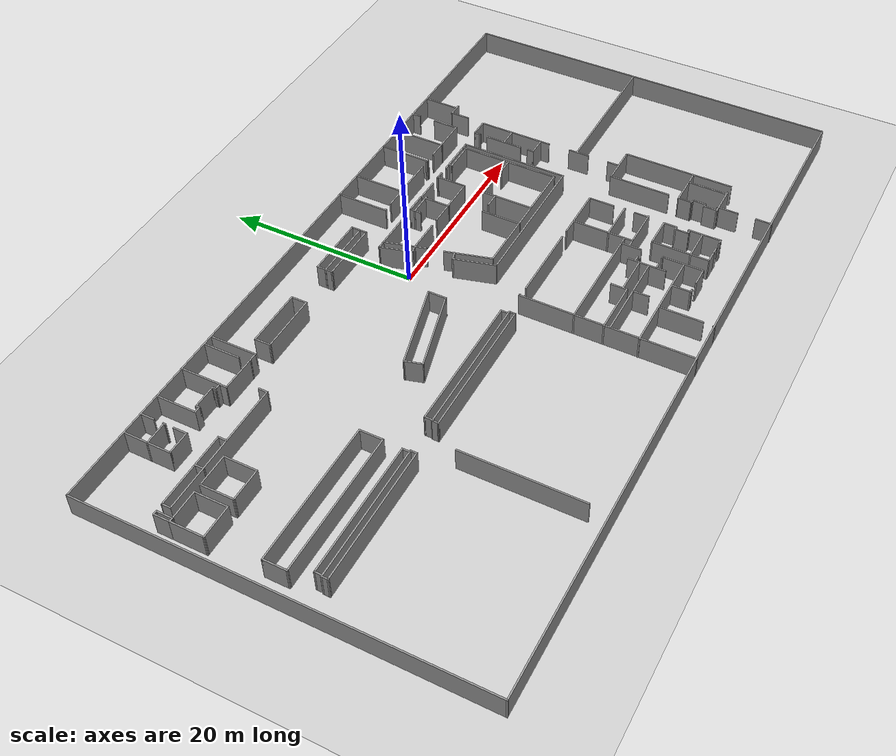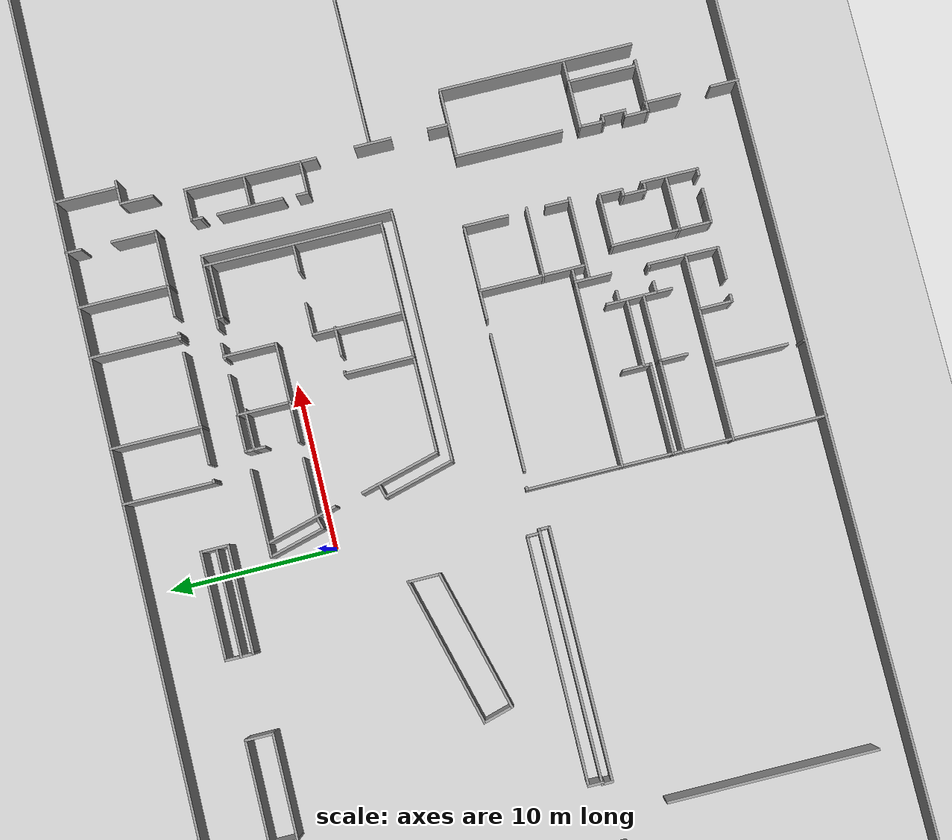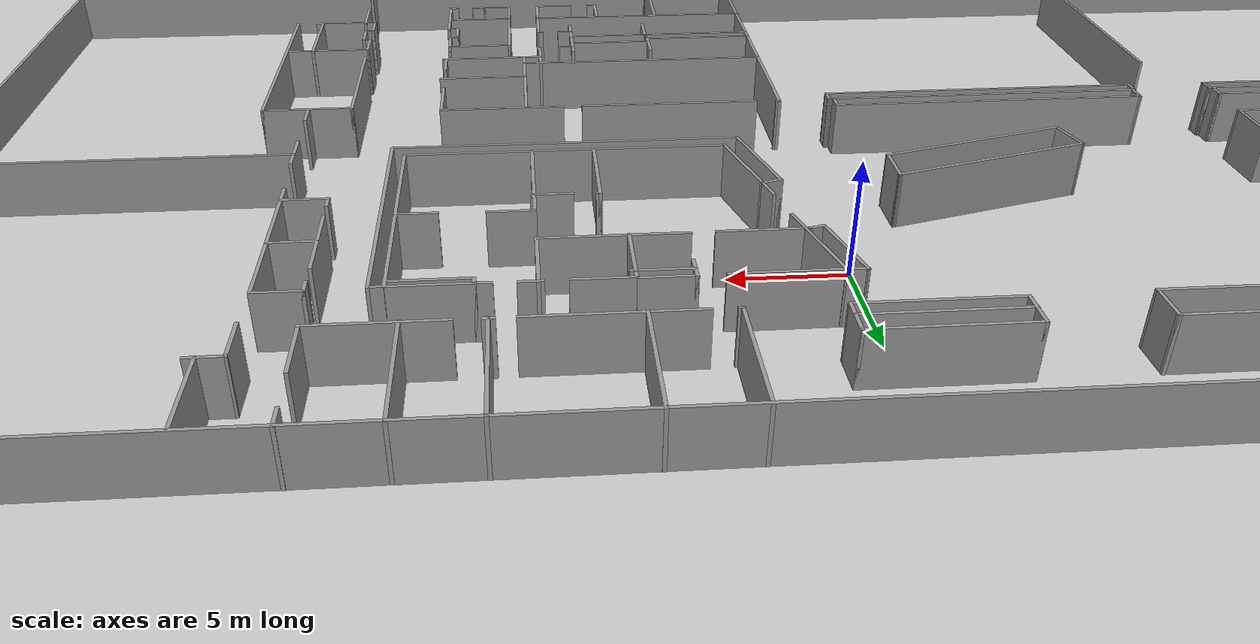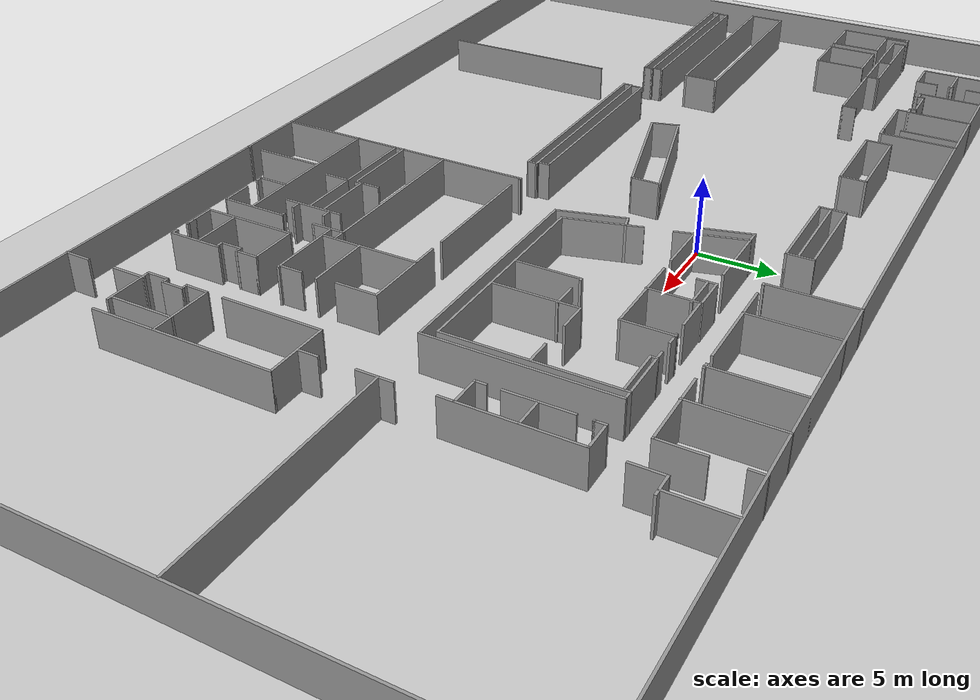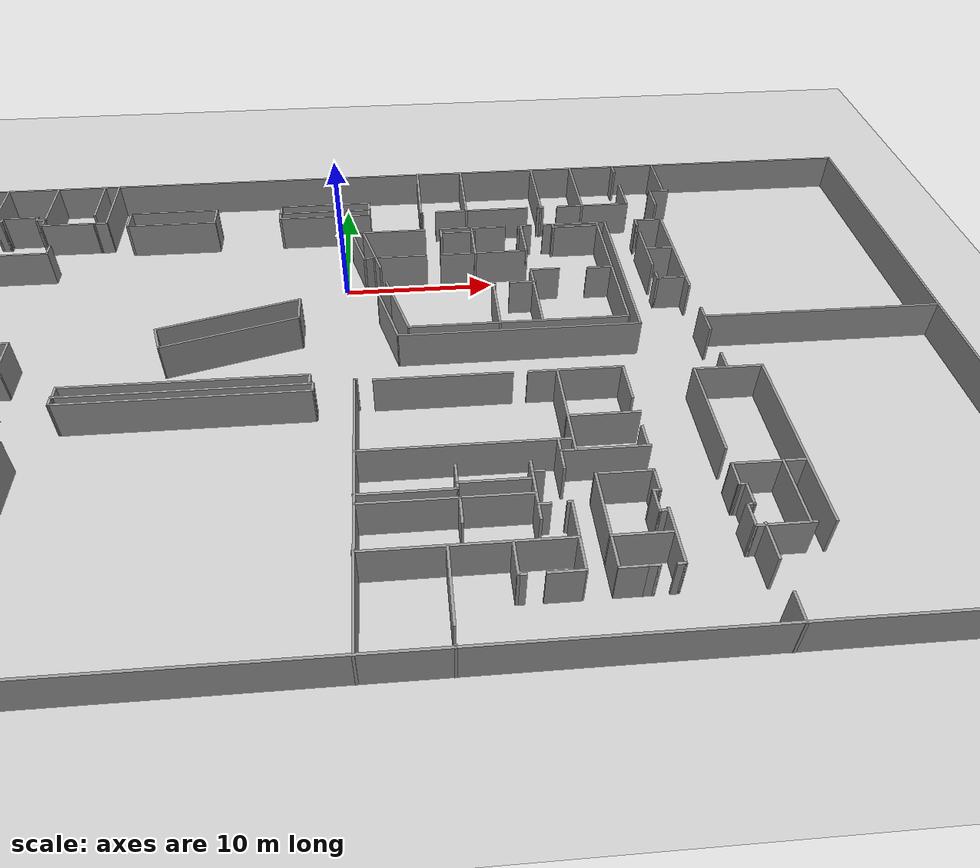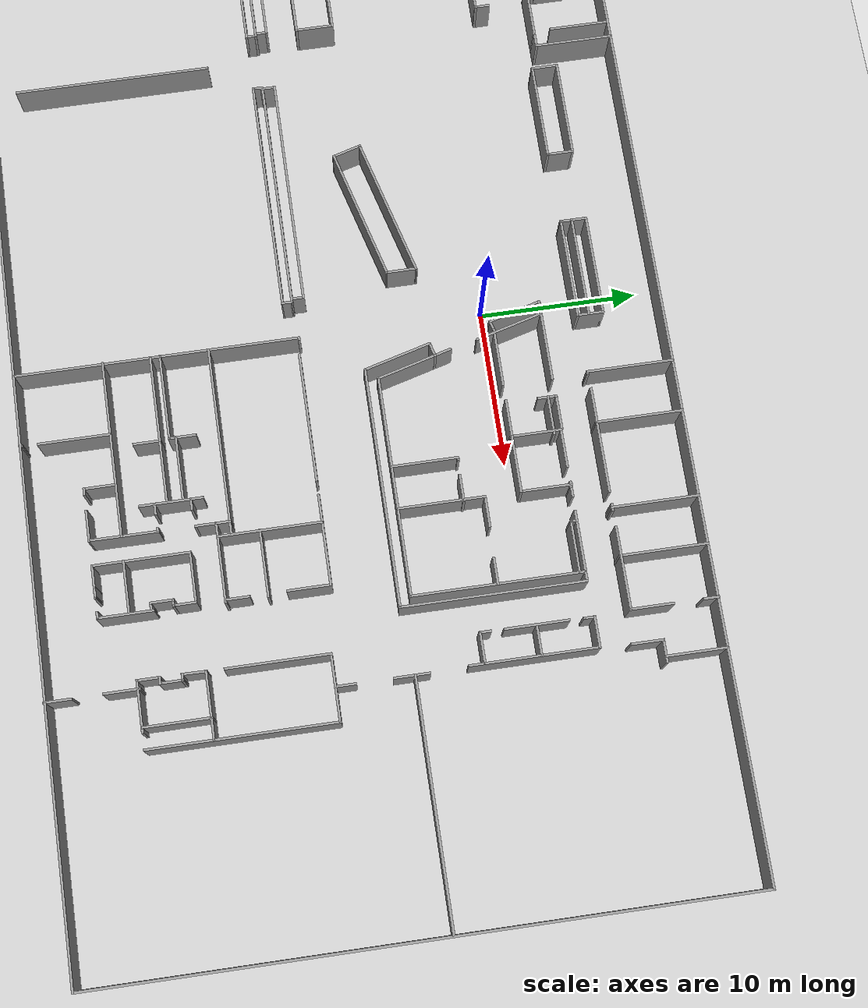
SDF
<sdf version="1.7">
 <world name="default">
  <light name="sun" type="directional">
   <pose>0 0 10 0 -0 0</pose>
   <diffuse>0.8 0.8 0.8 1</diffuse>
   <specular>0.2 0.2 0.2 1</specular>
   <attenuation>
    <range>1000</range>
    <constant>0.9</constant>
    <linear>0.01</linear>
    <quadratic>0.001</quadratic>
   </attenuation>
   <direction>-0.5 0.1 -0.9</direction>
   <spot><inner_angle>0</inner_angle><outer_angle>0</outer_angle><falloff>0</falloff></spot>
  </light>
  <model name="ground_plane">
   <static>1</static>
   <link name="link">
    <collision name="collision">
     <geometry><plane><normal>0 0 1</normal><size>100 100</size></plane></geometry>
     <surface>
      <contact><collide_bitmask>65535</collide_bitmask></contact>
      <friction><ode><mu>100</mu><mu2>50</mu2></ode></friction>
     </surface>
    </collision>
    <visual name="visual">
     <cast_shadows>0</cast_shadows>
     <geometry><plane><normal>0 0 1</normal><size>100 100</size></plane></geometry>
     <material>
      <script><uri>file://media/materials/scripts/gazebo.material</uri><name>Gazebo/Grey</name></script>
     </material>
    </visual>
   </link>
  </model>
  <gravity>0 0 -9.8</gravity>
  <magnetic_field>6e-06 2.3e-05 -4.2e-05</magnetic_field>
  <atmosphere type="adiabatic"/>
  <physics type="ode">
   <max_step_size>0.001</max_step_size>
   <real_time_factor>1</real_time_factor>
   <real_time_update_rate>1000</real_time_update_rate>
  </physics>
  <scene><ambient>0.4 0.4 0.4 1</ambient><background>0.7 0.7 0.7 1</background><shadows>1</shadows></scene>
  <spherical_coordinates>
   <surface_model>EARTH_WGS84</surface_model>
   <latitude_deg>0</latitude_deg>
   <longitude_deg>0</longitude_deg>
   <elevation>0</elevation>
   <heading_deg>0</heading_deg>
  </spherical_coordinates>
  <model name="gix_2f">
   <pose>0.287504 -9.19255 0 0 -0 0</pose>
   <link name="Wall_104">
    <collision name="Wall_104_Collision">
     <geometry><box><size>5.25 0.15 2.5</size></box></geometry>
     <pose>0 0 1.25 0 -0 0</pose>
    </collision>
    <visual name="Wall_104_Visual">
     <pose>0 0 1.25 0 -0 0</pose>
     <geometry><box><size>5.25 0.15 2.5</size></box></geometry>
     <material>
      <script><uri>file://media/materials/scripts/gazebo.material</uri><name>Gazebo/Grey</name></script>
      <ambient>1 1 1 1</ambient>
     </material>
     <meta><layer>0</layer></meta>
    </visual>
    <pose>17.6956 14.9975 0 0 -0 0</pose>
   </link>
   <link name="Wall_105">
    <collision name="Wall_105_Collision">
     <geometry><box><size>2.75 0.15 2.5</size></box></geometry>
     <pose>0 0 1.25 0 -0 0</pose>
    </collision>
    <visual name="Wall_105_Visual">
     <pose>0 0 1.25 0 -0 0</pose>
     <geometry><box><size>2.75 0.15 2.5</size></box></geometry>
     <material>
      <script><uri>file://media/materials/scripts/gazebo.material</uri><name>Gazebo/Grey</name></script>
      <ambient>1 1 1 1</ambient>
     </material>
     <meta><layer>0</layer></meta>
    </visual>
    <pose>20.2456 16.2975 0 0 -0 1.5708</pose>
   </link>
   <link name="Wall_107">
    <collision name="Wall_107_Collision">
     <geometry><box><size>1 0.15 2.5</size></box></geometry>
     <pose>0 0 1.25 0 -0 0</pose>
    </collision>
    <visual name="Wall_107_Visual">
     <pose>0 0 1.25 0 -0 0</pose>
     <geometry><box><size>1 0.15 2.5</size></box></geometry>
     <material>
      <script><uri>file://media/materials/scripts/gazebo.material</uri><name>Gazebo/Grey</name></script>
      <ambient>1 1 1 1</ambient>
     </material>
     <meta><layer>0</layer></meta>
    </visual>
    <pose>20.2383 19.9081 0 0 -0 -1.5708</pose>
   </link>
   <link name="Wall_109">
    <collision name="Wall_109_Collision">
     <geometry><box><size>5.5 0.15 2.5</size></box></geometry>
     <pose>0 0 1.25 0 -0 0</pose>
    </collision>
    <visual name="Wall_109_Visual">
     <pose>0 0 1.25 0 -0 0</pose>
     <geometry><box><size>5.5 0.15 2.5</size></box></geometry>
     <material>
      <script><uri>file://media/materials/scripts/gazebo.material</uri><name>Gazebo/Grey</name></script>
      <ambient>1 1 1 1</ambient>
     </material>
     <meta><layer>0</layer></meta>
    </visual>
    <pose>16.9145 17.64 0 0 -0 -1.5708</pose>
   </link>
   <link name="Wall_11">
    <collision name="Wall_11_Collision">
     <geometry><box><size>15 0.15 2.5</size></box></geometry>
     <pose>0 0 1.25 0 -0 0</pose>
    </collision>
    <visual name="Wall_11_Visual">
     <pose>0 0 1.25 0 -0 0</pose>
     <geometry><box><size>15 0.15 2.5</size></box></geometry>
     <material>
      <script><uri>file://media/materials/scripts/gazebo.material</uri><name>Gazebo/Grey</name></script>
      <ambient>1 1 1 1</ambient>
     </material>
     <meta><layer>0</layer></meta>
    </visual>
    <pose>-9.43001 -2.59263 0 0 -0 0</pose>
   </link>
   <link name="Wall_113">
    <collision name="Wall_113_Collision">
     <geometry><box><size>3.75 0.15 2.5</size></box></geometry>
     <pose>0 0 1.25 0 -0 0</pose>
    </collision>
    <visual name="Wall_113_Visual">
     <pose>0 0 1.25 0 -0 0</pose>
     <geometry><box><size>3.75 0.15 2.5</size></box></geometry>
     <material>
      <script><uri>file://media/materials/scripts/gazebo.material</uri><name>Gazebo/Grey</name></script>
      <ambient>1 1 1 1</ambient>
     </material>
     <meta><layer>0</layer></meta>
    </visual>
    <pose>23.3339 18.431 0 0 -0 1.5708</pose>
   </link>
   <link name="Wall_116">
    <collision name="Wall_116_Collision">
     <geometry><box><size>1.5 0.15 2.5</size></box></geometry>
     <pose>0 0 1.25 0 -0 0</pose>
    </collision>
    <visual name="Wall_116_Visual">
     <pose>0 0 1.25 0 -0 0</pose>
     <geometry><box><size>1.5 0.15 2.5</size></box></geometry>
     <material>
      <script><uri>file://media/materials/scripts/gazebo.material</uri><name>Gazebo/Grey</name></script>
      <ambient>1 1 1 1</ambient>
     </material>
     <meta><layer>0</layer></meta>
    </visual>
    <pose>23.0121 16.5984 0 0 -0 0</pose>
   </link>
   <link name="Wall_118">
    <collision name="Wall_118_Collision">
     <geometry><box><size>2.0449 0.15 2.5</size></box></geometry>
     <pose>0 0 1.25 0 -0 0</pose>
    </collision>
    <visual name="Wall_118_Visual">
     <pose>0 0 1.25 0 -0 0</pose>
     <geometry><box><size>2.0449 0.15 2.5</size></box></geometry>
     <material>
      <script><uri>file://media/materials/scripts/gazebo.material</uri><name>Gazebo/Grey</name></script>
      <ambient>1 1 1 1</ambient>
     </material>
     <meta><layer>0</layer></meta>
    </visual>
    <pose>22.3357 15.651 0 0 -0 1.5693</pose>
   </link>
   <link name="Wall_12">
    <collision name="Wall_12_Collision">
     <geometry><box><size>0.747125 0.15 2.5</size></box></geometry>
     <pose>0 0 1.25 0 -0 0</pose>
    </collision>
    <visual name="Wall_12_Visual">
     <pose>0 0 1.25 0 -0 0</pose>
     <geometry><box><size>0.747125 0.15 2.5</size></box></geometry>
     <material>
      <script><uri>file://media/materials/scripts/gazebo.material</uri><name>Gazebo/Grey</name></script>
      <ambient>1 1 1 1</ambient>
     </material>
     <meta><layer>0</layer></meta>
    </visual>
    <pose>-2.00806 -2.89118 0 0 -0 -1.58103</pose>
   </link>
   <link name="Wall_120">
    <collision name="Wall_120_Collision">
     <geometry><box><size>0.16 0.15 2.5</size></box></geometry>
     <pose>0 0 1.25 0 -0 0</pose>
    </collision>
    <visual name="Wall_120_Visual">
     <pose>0 0 1.25 0 -0 0</pose>
     <geometry><box><size>0.16 0.15 2.5</size></box></geometry>
     <material>
      <script><uri>file://media/materials/scripts/gazebo.material</uri><name>Gazebo/Grey</name></script>
      <ambient>1 1 1 1</ambient>
     </material>
     <meta><layer>0</layer></meta>
    </visual>
    <pose>20.3829 12.1748 0 0 -0 0</pose>
   </link>
   <link name="Wall_121">
    <collision name="Wall_121_Collision">
     <geometry><box><size>0.75 0.15 2.5</size></box></geometry>
     <pose>0 0 1.25 0 -0 0</pose>
    </collision>
    <visual name="Wall_121_Visual">
     <pose>0 0 1.25 0 -0 0</pose>
     <geometry><box><size>0.75 0.15 2.5</size></box></geometry>
     <material>
      <script><uri>file://media/materials/scripts/gazebo.material</uri><name>Gazebo/Grey</name></script>
      <ambient>1 1 1 1</ambient>
     </material>
     <meta><layer>0</layer></meta>
    </visual>
    <pose>20.3879 12.4748 0 0 -0 1.5708</pose>
   </link>
   <link name="Wall_122">
    <collision name="Wall_122_Collision">
     <geometry><box><size>2 0.15 2.5</size></box></geometry>
     <pose>0 0 1.25 0 -0 0</pose>
    </collision>
    <visual name="Wall_122_Visual">
     <pose>0 0 1.25 0 -0 0</pose>
     <geometry><box><size>2 0.15 2.5</size></box></geometry>
     <material>
      <script><uri>file://media/materials/scripts/gazebo.material</uri><name>Gazebo/Grey</name></script>
      <ambient>1 1 1 1</ambient>
     </material>
     <meta><layer>0</layer></meta>
    </visual>
    <pose>21.3129 12.7748 0 0 -0 0</pose>
   </link>
   <link name="Wall_123">
    <collision name="Wall_123_Collision">
     <geometry><box><size>8 0.15 2.5</size></box></geometry>
     <pose>0 0 1.25 0 -0 0</pose>
    </collision>
    <visual name="Wall_123_Visual">
     <pose>0 0 1.25 0 -0 0</pose>
     <geometry><box><size>8 0.15 2.5</size></box></geometry>
     <material>
      <script><uri>file://media/materials/scripts/gazebo.material</uri><name>Gazebo/Grey</name></script>
      <ambient>1 1 1 1</ambient>
     </material>
     <meta><layer>0</layer></meta>
    </visual>
    <pose>22.2379 8.84977 0 0 -0 -1.5708</pose>
   </link>
   <link name="Wall_125">
    <collision name="Wall_125_Collision">
     <geometry><box><size>4 0.15 2.5</size></box></geometry>
     <pose>0 0 1.25 0 -0 0</pose>
    </collision>
    <visual name="Wall_125_Visual">
     <pose>0 0 1.25 0 -0 0</pose>
     <geometry><box><size>4 0.15 2.5</size></box></geometry>
     <material>
      <script><uri>file://media/materials/scripts/gazebo.material</uri><name>Gazebo/Grey</name></script>
      <ambient>1 1 1 1</ambient>
     </material>
     <meta><layer>0</layer></meta>
    </visual>
    <pose>20.3613 9.28577 0 0 -0 -1.5708</pose>
   </link>
   <link name="Wall_127">
    <collision name="Wall_127_Collision">
     <geometry><box><size>0.75 0.15 2.5</size></box></geometry>
     <pose>0 0 1.25 0 -0 0</pose>
    </collision>
    <visual name="Wall_127_Visual">
     <pose>0 0 1.25 0 -0 0</pose>
     <geometry><box><size>0.75 0.15 2.5</size></box></geometry>
     <material>
      <script><uri>file://media/materials/scripts/gazebo.material</uri><name>Gazebo/Grey</name></script>
      <ambient>1 1 1 1</ambient>
     </material>
     <meta><layer>0</layer></meta>
    </visual>
    <pose>20.3565 6.14583 0 0 -0 -1.5708</pose>
   </link>
   <link name="Wall_128">
    <collision name="Wall_128_Collision">
     <geometry><box><size>2 0.15 2.5</size></box></geometry>
     <pose>0 0 1.25 0 -0 0</pose>
    </collision>
    <visual name="Wall_128_Visual">
     <pose>0 0 1.25 0 -0 0</pose>
     <geometry><box><size>2 0.15 2.5</size></box></geometry>
     <material>
      <script><uri>file://media/materials/scripts/gazebo.material</uri><name>Gazebo/Grey</name></script>
      <ambient>1 1 1 1</ambient>
     </material>
     <meta><layer>0</layer></meta>
    </visual>
    <pose>21.2815 5.84583 0 0 -0 0</pose>
   </link>
   <link name="Wall_13">
    <collision name="Wall_13_Collision">
     <geometry><box><size>15 0.15 2.5</size></box></geometry>
     <pose>0 0 1.25 0 -0 0</pose>
    </collision>
    <visual name="Wall_13_Visual">
     <pose>0 0 1.25 0 -0 0</pose>
     <geometry><box><size>15 0.15 2.5</size></box></geometry>
     <material>
      <script><uri>file://media/materials/scripts/gazebo.material</uri><name>Gazebo/Grey</name></script>
      <ambient>1 1 1 1</ambient>
     </material>
     <meta><layer>0</layer></meta>
    </visual>
    <pose>-9.43612 -3.18973 0 0 -0 3.14159</pose>
   </link>
   <link name="Wall_130">
    <collision name="Wall_130_Collision">
     <geometry><box><size>2 0.15 2.5</size></box></geometry>
     <pose>0 0 1.25 0 -0 0</pose>
    </collision>
    <visual name="Wall_130_Visual">
     <pose>0 0 1.25 0 -0 0</pose>
     <geometry><box><size>2 0.15 2.5</size></box></geometry>
     <material>
      <script><uri>file://media/materials/scripts/gazebo.material</uri><name>Gazebo/Grey</name></script>
      <ambient>1 1 1 1</ambient>
     </material>
     <meta><layer>0</layer></meta>
    </visual>
    <pose>21.2959 9.26453 0 0 -0 0</pose>
   </link>
   <link name="Wall_132">
    <collision name="Wall_132_Collision">
     <geometry><box><size>2.25 0.15 2.5</size></box></geometry>
     <pose>0 0 1.25 0 -0 0</pose>
    </collision>
    <visual name="Wall_132_Visual">
     <pose>0 0 1.25 0 -0 0</pose>
     <geometry><box><size>2.25 0.15 2.5</size></box></geometry>
     <material>
      <script><uri>file://media/materials/scripts/gazebo.material</uri><name>Gazebo/Grey</name></script>
      <ambient>1 1 1 1</ambient>
     </material>
     <meta><layer>0</layer></meta>
    </visual>
    <pose>22.3373 1.44229 0 0 -0 -1.5708</pose>
   </link>
   <link name="Wall_134">
    <collision name="Wall_134_Collision">
     <geometry><box><size>15.25 0.15 2.5</size></box></geometry>
     <pose>0 0 1.25 0 -0 0</pose>
    </collision>
    <visual name="Wall_134_Visual">
     <pose>0 0 1.25 0 -0 0</pose>
     <geometry><box><size>15.25 0.15 2.5</size></box></geometry>
     <material>
      <script><uri>file://media/materials/scripts/gazebo.material</uri><name>Gazebo/Grey</name></script>
      <ambient>1 1 1 1</ambient>
     </material>
     <meta><layer>0</layer></meta>
    </visual>
    <pose>29.9039 1.64609 0 0 -0 0</pose>
   </link>
   <link name="Wall_136">
    <collision name="Wall_136_Collision">
     <geometry><box><size>6.5 0.15 2.5</size></box></geometry>
     <pose>0 0 1.25 0 -0 0</pose>
    </collision>
    <visual name="Wall_136_Visual">
     <pose>0 0 1.25 0 -0 0</pose>
     <geometry><box><size>6.5 0.15 2.5</size></box></geometry>
     <material>
      <script><uri>file://media/materials/scripts/gazebo.material</uri><name>Gazebo/Grey</name></script>
      <ambient>1 1 1 1</ambient>
     </material>
     <meta><layer>0</layer></meta>
    </visual>
    <pose>20.356 -6.31962 0 0 -0 1.5708</pose>
   </link>
   <link name="Wall_137">
    <collision name="Wall_137_Collision">
     <geometry><box><size>4.25 0.15 2.5</size></box></geometry>
     <pose>0 0 1.25 0 -0 0</pose>
    </collision>
    <visual name="Wall_137_Visual">
     <pose>0 0 1.25 0 -0 0</pose>
     <geometry><box><size>4.25 0.15 2.5</size></box></geometry>
     <material>
      <script><uri>file://media/materials/scripts/gazebo.material</uri><name>Gazebo/Grey</name></script>
      <ambient>1 1 1 1</ambient>
     </material>
     <meta><layer>0</layer></meta>
    </visual>
    <pose>22.406 -3.14462 0 0 -0 0</pose>
   </link>
   <link name="Wall_138">
    <collision name="Wall_138_Collision">
     <geometry><box><size>11.75 0.15 2.5</size></box></geometry>
     <pose>0 0 1.25 0 -0 0</pose>
    </collision>
    <visual name="Wall_138_Visual">
     <pose>0 0 1.25 0 -0 0</pose>
     <geometry><box><size>11.75 0.15 2.5</size></box></geometry>
     <material>
      <script><uri>file://media/materials/scripts/gazebo.material</uri><name>Gazebo/Grey</name></script>
      <ambient>1 1 1 1</ambient>
     </material>
     <meta><layer>0</layer></meta>
    </visual>
    <pose>24.456 -8.94462 0 0 -0 -1.5708</pose>
   </link>
   <link name="Wall_14">
    <collision name="Wall_14_Collision">
     <geometry><box><size>0.747125 0.15 2.5</size></box></geometry>
     <pose>0 0 1.25 0 -0 0</pose>
    </collision>
    <visual name="Wall_14_Visual">
     <pose>0 0 1.25 0 -0 0</pose>
     <geometry><box><size>0.747125 0.15 2.5</size></box></geometry>
     <material>
      <script><uri>file://media/materials/scripts/gazebo.material</uri><name>Gazebo/Grey</name></script>
      <ambient>1 1 1 1</ambient>
     </material>
     <meta><layer>0</layer></meta>
    </visual>
    <pose>-16.8581 -2.89118 0 0 -0 1.56056</pose>
   </link>
   <link name="Wall_140">
    <collision name="Wall_140_Collision">
     <geometry><box><size>1.25 0.15 2.5</size></box></geometry>
     <pose>0 0 1.25 0 -0 0</pose>
    </collision>
    <visual name="Wall_140_Visual">
     <pose>0 0 1.25 0 -0 0</pose>
     <geometry><box><size>1.25 0.15 2.5</size></box></geometry>
     <material>
      <script><uri>file://media/materials/scripts/gazebo.material</uri><name>Gazebo/Grey</name></script>
      <ambient>1 1 1 1</ambient>
     </material>
     <meta><layer>0</layer></meta>
    </visual>
    <pose>22.3435 -2.49513 0 0 -0 -1.5708</pose>
   </link>
   <link name="Wall_142">
    <collision name="Wall_142_Collision">
     <geometry><box><size>4.25 0.15 2.5</size></box></geometry>
     <pose>0 0 1.25 0 -0 0</pose>
    </collision>
    <visual name="Wall_142_Visual">
     <pose>0 0 1.25 0 -0 0</pose>
     <geometry><box><size>4.25 0.15 2.5</size></box></geometry>
     <material>
      <script><uri>file://media/materials/scripts/gazebo.material</uri><name>Gazebo/Grey</name></script>
      <ambient>1 1 1 1</ambient>
     </material>
     <meta><layer>0</layer></meta>
    </visual>
    <pose>22.396 -10.6333 0 0 -0 0</pose>
   </link>
   <link name="Wall_144">
    <collision name="Wall_144_Collision">
     <geometry><box><size>3.25 0.15 2.5</size></box></geometry>
     <pose>0 0 1.25 0 -0 0</pose>
    </collision>
    <visual name="Wall_144_Visual">
     <pose>0 0 1.25 0 -0 0</pose>
     <geometry><box><size>3.25 0.15 2.5</size></box></geometry>
     <material>
      <script><uri>file://media/materials/scripts/gazebo.material</uri><name>Gazebo/Grey</name></script>
      <ambient>1 1 1 1</ambient>
     </material>
     <meta><layer>0</layer></meta>
    </visual>
    <pose>21.8553 -14.7544 0 0 -0 3.14159</pose>
   </link>
   <link name="Wall_145">
    <collision name="Wall_145_Collision">
     <geometry><box><size>0.16 0.15 2.5</size></box></geometry>
     <pose>0 0 1.25 0 -0 0</pose>
    </collision>
    <visual name="Wall_145_Visual">
     <pose>0 0 1.25 0 -0 0</pose>
     <geometry><box><size>0.16 0.15 2.5</size></box></geometry>
     <material>
      <script><uri>file://media/materials/scripts/gazebo.material</uri><name>Gazebo/Grey</name></script>
      <ambient>1 1 1 1</ambient>
     </material>
     <meta><layer>0</layer></meta>
    </visual>
    <pose>20.3103 -14.7544 0 0 -0 0</pose>
   </link>
   <link name="Wall_146">
    <collision name="Wall_146_Collision">
     <geometry><box><size>1.5 0.15 2.5</size></box></geometry>
     <pose>0 0 1.25 0 -0 0</pose>
    </collision>
    <visual name="Wall_146_Visual">
     <pose>0 0 1.25 0 -0 0</pose>
     <geometry><box><size>1.5 0.15 2.5</size></box></geometry>
     <material>
      <script><uri>file://media/materials/scripts/gazebo.material</uri><name>Gazebo/Grey</name></script>
      <ambient>1 1 1 1</ambient>
     </material>
     <meta><layer>0</layer></meta>
    </visual>
    <pose>20.3153 -14.0794 0 0 -0 1.5708</pose>
   </link>
   <link name="Wall_147">
    <collision name="Wall_147_Collision">
     <geometry><box><size>0.5 0.15 2.5</size></box></geometry>
     <pose>0 0 1.25 0 -0 0</pose>
    </collision>
    <visual name="Wall_147_Visual">
     <pose>0 0 1.25 0 -0 0</pose>
     <geometry><box><size>0.5 0.15 2.5</size></box></geometry>
     <material>
      <script><uri>file://media/materials/scripts/gazebo.material</uri><name>Gazebo/Grey</name></script>
      <ambient>1 1 1 1</ambient>
     </material>
     <meta><layer>0</layer></meta>
    </visual>
    <pose>20.4903 -13.4044 0 0 -0 0</pose>
   </link>
   <link name="Wall_148">
    <collision name="Wall_148_Collision">
     <geometry><box><size>0.16 0.15 2.5</size></box></geometry>
     <pose>0 0 1.25 0 -0 0</pose>
    </collision>
    <visual name="Wall_148_Visual">
     <pose>0 0 1.25 0 -0 0</pose>
     <geometry><box><size>0.16 0.15 2.5</size></box></geometry>
     <material>
      <script><uri>file://media/materials/scripts/gazebo.material</uri><name>Gazebo/Grey</name></script>
      <ambient>1 1 1 1</ambient>
     </material>
     <meta><layer>0</layer></meta>
    </visual>
    <pose>20.6703 -13.4044 0 0 -0 0</pose>
   </link>
   <link name="Wall_149">
    <collision name="Wall_149_Collision">
     <geometry><box><size>1.5 0.15 2.5</size></box></geometry>
     <pose>0 0 1.25 0 -0 0</pose>
    </collision>
    <visual name="Wall_149_Visual">
     <pose>0 0 1.25 0 -0 0</pose>
     <geometry><box><size>1.5 0.15 2.5</size></box></geometry>
     <material>
      <script><uri>file://media/materials/scripts/gazebo.material</uri><name>Gazebo/Grey</name></script>
      <ambient>1 1 1 1</ambient>
     </material>
     <meta><layer>0</layer></meta>
    </visual>
    <pose>20.6753 -12.7294 0 0 -0 1.5708</pose>
   </link>
   <link name="Wall_150">
    <collision name="Wall_150_Collision">
     <geometry><box><size>0.5 0.15 2.5</size></box></geometry>
     <pose>0 0 1.25 0 -0 0</pose>
    </collision>
    <visual name="Wall_150_Visual">
     <pose>0 0 1.25 0 -0 0</pose>
     <geometry><box><size>0.5 0.15 2.5</size></box></geometry>
     <material>
      <script><uri>file://media/materials/scripts/gazebo.material</uri><name>Gazebo/Grey</name></script>
      <ambient>1 1 1 1</ambient>
     </material>
     <meta><layer>0</layer></meta>
    </visual>
    <pose>20.5003 -12.0544 0 0 -0 3.14159</pose>
   </link>
   <link name="Wall_151">
    <collision name="Wall_151_Collision">
     <geometry><box><size>1.57121 0.15 2.5</size></box></geometry>
     <pose>0 0 1.25 0 -0 0</pose>
    </collision>
    <visual name="Wall_151_Visual">
     <pose>0 0 1.25 0 -0 0</pose>
     <geometry><box><size>1.57121 0.15 2.5</size></box></geometry>
     <material>
      <script><uri>file://media/materials/scripts/gazebo.material</uri><name>Gazebo/Grey</name></script>
      <ambient>1 1 1 1</ambient>
     </material>
     <meta><layer>0</layer></meta>
    </visual>
    <pose>20.3357 -11.3438 0 0 -0 1.55622</pose>
   </link>
   <link name="Wall_154">
    <collision name="Wall_154_Collision">
     <geometry><box><size>4.25 0.15 2.5</size></box></geometry>
     <pose>0 0 1.25 0 -0 0</pose>
    </collision>
    <visual name="Wall_154_Visual">
     <pose>0 0 1.25 0 -0 0</pose>
     <geometry><box><size>4.25 0.15 2.5</size></box></geometry>
     <material>
      <script><uri>file://media/materials/scripts/gazebo.material</uri><name>Gazebo/Grey</name></script>
      <ambient>1 1 1 1</ambient>
     </material>
     <meta><layer>0</layer></meta>
    </visual>
    <pose>23.129 -12.6736 0 0 -0 -1.5708</pose>
   </link>
   <link name="Wall_156">
    <collision name="Wall_156_Collision">
     <geometry><box><size>2.25 0.15 2.5</size></box></geometry>
     <pose>0 0 1.25 0 -0 0</pose>
    </collision>
    <visual name="Wall_156_Visual">
     <pose>0 0 1.25 0 -0 0</pose>
     <geometry><box><size>2.25 0.15 2.5</size></box></geometry>
     <material>
      <script><uri>file://media/materials/scripts/gazebo.material</uri><name>Gazebo/Grey</name></script>
      <ambient>1 1 1 1</ambient>
     </material>
     <meta><layer>0</layer></meta>
    </visual>
    <pose>20.826 -15.7164 0 0 -0 1.5708</pose>
   </link>
   <link name="Wall_158">
    <collision name="Wall_158_Collision">
     <geometry><box><size>1.75 0.15 2.5</size></box></geometry>
     <pose>0 0 1.25 0 -0 0</pose>
    </collision>
    <visual name="Wall_158_Visual">
     <pose>0 0 1.25 0 -0 0</pose>
     <geometry><box><size>1.75 0.15 2.5</size></box></geometry>
     <material>
      <script><uri>file://media/materials/scripts/gazebo.material</uri><name>Gazebo/Grey</name></script>
      <ambient>1 1 1 1</ambient>
     </material>
     <meta><layer>0</layer></meta>
    </visual>
    <pose>20.8495 -19.5331 0 0 -0 -1.5708</pose>
   </link>
   <link name="Wall_16">
    <collision name="Wall_16_Collision">
     <geometry><box><size>40.75 0.15 2.5</size></box></geometry>
     <pose>0 0 1.25 0 -0 0</pose>
    </collision>
    <visual name="Wall_16_Visual">
     <pose>0 0 1.25 0 -0 0</pose>
     <geometry><box><size>40.75 0.15 2.5</size></box></geometry>
     <material>
      <script><uri>file://media/materials/scripts/gazebo.material</uri><name>Gazebo/Grey</name></script>
      <ambient>1 1 1 1</ambient>
     </material>
     <meta><layer>0</layer></meta>
    </visual>
    <pose>-37.55 0.010736 0 0 -0 1.5708</pose>
   </link>
   <link name="Wall_160">
    <collision name="Wall_160_Collision">
     <geometry><box><size>18 0.15 2.5</size></box></geometry>
     <pose>0 0 1.25 0 -0 0</pose>
    </collision>
    <visual name="Wall_160_Visual">
     <pose>0 0 1.25 0 -0 0</pose>
     <geometry><box><size>18 0.15 2.5</size></box></geometry>
     <material>
      <script><uri>file://media/materials/scripts/gazebo.material</uri><name>Gazebo/Grey</name></script>
      <ambient>1 1 1 1</ambient>
     </material>
     <meta><layer>0</layer></meta>
    </visual>
    <pose>0.398763 -11.388 0 0 -0 1.5708</pose>
   </link>
   <link name="Wall_161">
    <collision name="Wall_161_Collision">
     <geometry><box><size>0.25 0.15 2.5</size></box></geometry>
     <pose>0 0 1.25 0 -0 0</pose>
    </collision>
    <visual name="Wall_161_Visual">
     <pose>0 0 1.25 0 -0 0</pose>
     <geometry><box><size>0.25 0.15 2.5</size></box></geometry>
     <material>
      <script><uri>file://media/materials/scripts/gazebo.material</uri><name>Gazebo/Grey</name></script>
      <ambient>1 1 1 1</ambient>
     </material>
     <meta><layer>0</layer></meta>
    </visual>
    <pose>0.448763 -2.46302 0 0 -0 0</pose>
   </link>
   <link name="Wall_164">
    <collision name="Wall_164_Collision">
     <geometry><box><size>8.25 0.15 2.5</size></box></geometry>
     <pose>0 0 1.25 0 -0 0</pose>
    </collision>
    <visual name="Wall_164_Visual">
     <pose>0 0 1.25 0 -0 0</pose>
     <geometry><box><size>8.25 0.15 2.5</size></box></geometry>
     <material>
      <script><uri>file://media/materials/scripts/gazebo.material</uri><name>Gazebo/Grey</name></script>
      <ambient>1 1 1 1</ambient>
     </material>
     <meta><layer>0</layer></meta>
    </visual>
    <pose>5.57058 -2.58584 0 0 -0 0</pose>
   </link>
   <link name="Wall_168">
    <collision name="Wall_168_Collision">
     <geometry><box><size>5.75 0.15 2.5</size></box></geometry>
     <pose>0 0 1.25 0 -0 0</pose>
    </collision>
    <visual name="Wall_168_Visual">
     <pose>0 0 1.25 0 -0 0</pose>
     <geometry><box><size>5.75 0.15 2.5</size></box></geometry>
     <material>
      <script><uri>file://media/materials/scripts/gazebo.material</uri><name>Gazebo/Grey</name></script>
      <ambient>1 1 1 1</ambient>
     </material>
     <meta><layer>0</layer></meta>
    </visual>
    <pose>13.4074 -2.59567 0 0 -0 0</pose>
   </link>
   <link name="Wall_169">
    <collision name="Wall_169_Collision">
     <geometry><box><size>2.75 0.15 2.5</size></box></geometry>
     <pose>0 0 1.25 0 -0 0</pose>
    </collision>
    <visual name="Wall_169_Visual">
     <pose>0 0 1.25 0 -0 0</pose>
     <geometry><box><size>2.75 0.15 2.5</size></box></geometry>
     <material>
      <script><uri>file://media/materials/scripts/gazebo.material</uri><name>Gazebo/Grey</name></script>
      <ambient>1 1 1 1</ambient>
     </material>
     <meta><layer>0</layer></meta>
    </visual>
    <pose>16.2074 -3.89568 0 0 -0 -1.5708</pose>
   </link>
   <link name="Wall_171">
    <collision name="Wall_171_Collision">
     <geometry><box><size>1.5 0.15 2.5</size></box></geometry>
     <pose>0 0 1.25 0 -0 0</pose>
    </collision>
    <visual name="Wall_171_Visual">
     <pose>0 0 1.25 0 -0 0</pose>
     <geometry><box><size>1.5 0.15 2.5</size></box></geometry>
     <material>
      <script><uri>file://media/materials/scripts/gazebo.material</uri><name>Gazebo/Grey</name></script>
      <ambient>1 1 1 1</ambient>
     </material>
     <meta><layer>0</layer></meta>
    </visual>
    <pose>16.2286 -8.22332 0 0 -0 -1.5708</pose>
   </link>
   <link name="Wall_174">
    <collision name="Wall_174_Collision">
     <geometry><box><size>6.5 0.15 2.5</size></box></geometry>
     <pose>0 0 1.25 0 -0 0</pose>
    </collision>
    <visual name="Wall_174_Visual">
     <pose>0 0 1.25 0 -0 0</pose>
     <geometry><box><size>6.5 0.15 2.5</size></box></geometry>
     <material>
      <script><uri>file://media/materials/scripts/gazebo.material</uri><name>Gazebo/Grey</name></script>
      <ambient>1 1 1 1</ambient>
     </material>
     <meta><layer>0</layer></meta>
    </visual>
    <pose>12.2884 -5.79752 0 0 -0 -1.5708</pose>
   </link>
   <link name="Wall_176">
    <collision name="Wall_176_Collision">
     <geometry><box><size>5 0.15 2.5</size></box></geometry>
     <pose>0 0 1.25 0 -0 0</pose>
    </collision>
    <visual name="Wall_176_Visual">
     <pose>0 0 1.25 0 -0 0</pose>
     <geometry><box><size>5 0.15 2.5</size></box></geometry>
     <material>
      <script><uri>file://media/materials/scripts/gazebo.material</uri><name>Gazebo/Grey</name></script>
      <ambient>1 1 1 1</ambient>
     </material>
     <meta><layer>0</layer></meta>
    </visual>
    <pose>13.9309 -8.97341 0 0 -0 0</pose>
   </link>
   <link name="Wall_178">
    <collision name="Wall_178_Collision">
     <geometry><box><size>4.25 0.15 2.5</size></box></geometry>
     <pose>0 0 1.25 0 -0 0</pose>
    </collision>
    <visual name="Wall_178_Visual">
     <pose>0 0 1.25 0 -0 0</pose>
     <geometry><box><size>4.25 0.15 2.5</size></box></geometry>
     <material>
      <script><uri>file://media/materials/scripts/gazebo.material</uri><name>Gazebo/Grey</name></script>
      <ambient>1 1 1 1</ambient>
     </material>
     <meta><layer>0</layer></meta>
    </visual>
    <pose>14.3197 -6.39481 0 0 -0 0</pose>
   </link>
   <link name="Wall_180">
    <collision name="Wall_180_Collision">
     <geometry><box><size>12 0.15 2.5</size></box></geometry>
     <pose>0 0 1.25 0 -0 0</pose>
    </collision>
    <visual name="Wall_180_Visual">
     <pose>0 0 1.25 0 -0 0</pose>
     <geometry><box><size>12 0.15 2.5</size></box></geometry>
     <material>
      <script><uri>file://media/materials/scripts/gazebo.material</uri><name>Gazebo/Grey</name></script>
      <ambient>1 1 1 1</ambient>
     </material>
     <meta><layer>0</layer></meta>
    </visual>
    <pose>6.32009 -8.12995 0 0 -0 0</pose>
   </link>
   <link name="Wall_182">
    <collision name="Wall_182_Collision">
     <geometry><box><size>2.25 0.15 2.5</size></box></geometry>
     <pose>0 0 1.25 0 -0 0</pose>
    </collision>
    <visual name="Wall_182_Visual">
     <pose>0 0 1.25 0 -0 0</pose>
     <geometry><box><size>2.25 0.15 2.5</size></box></geometry>
     <material>
      <script><uri>file://media/materials/scripts/gazebo.material</uri><name>Gazebo/Grey</name></script>
      <ambient>1 1 1 1</ambient>
     </material>
     <meta><layer>0</layer></meta>
    </visual>
    <pose>11.4573 -9.17497 0 0 -0 -1.5708</pose>
   </link>
   <link name="Wall_183">
    <collision name="Wall_183_Collision">
     <geometry><box><size>0.15 0.15 2.5</size></box></geometry>
     <pose>0 0 1.25 0 -0 0</pose>
    </collision>
    <visual name="Wall_183_Visual">
     <pose>0 0 1.25 0 -0 0</pose>
     <geometry><box><size>0.15 0.15 2.5</size></box></geometry>
     <material>
      <script><uri>file://media/materials/scripts/gazebo.material</uri><name>Gazebo/Grey</name></script>
      <ambient>1 1 1 1</ambient>
     </material>
     <meta><layer>0</layer></meta>
    </visual>
    <pose>11.4573 -10.225 0 0 -0 0</pose>
   </link>
   <link name="Wall_185">
    <collision name="Wall_185_Collision">
     <geometry><box><size>4 0.15 2.5</size></box></geometry>
     <pose>0 0 1.25 0 -0 0</pose>
    </collision>
    <visual name="Wall_185_Visual">
     <pose>0 0 1.25 0 -0 0</pose>
     <geometry><box><size>4 0.15 2.5</size></box></geometry>
     <material>
      <script><uri>file://media/materials/scripts/gazebo.material</uri><name>Gazebo/Grey</name></script>
      <ambient>1 1 1 1</ambient>
     </material>
     <meta><layer>0</layer></meta>
    </visual>
    <pose>9.73962 -11.5348 0 0 -0 -1.5708</pose>
   </link>
   <link name="Wall_187">
    <collision name="Wall_187_Collision">
     <geometry><box><size>0.75 0.15 2.5</size></box></geometry>
     <pose>0 0 1.25 0 -0 0</pose>
    </collision>
    <visual name="Wall_187_Visual">
     <pose>0 0 1.25 0 -0 0</pose>
     <geometry><box><size>0.75 0.15 2.5</size></box></geometry>
     <material>
      <script><uri>file://media/materials/scripts/gazebo.material</uri><name>Gazebo/Grey</name></script>
      <ambient>1 1 1 1</ambient>
     </material>
     <meta><layer>0</layer></meta>
    </visual>
    <pose>10.0453 -10.3188 0 0 -0 0</pose>
   </link>
   <link name="Wall_189">
    <collision name="Wall_189_Collision">
     <geometry><box><size>0.75 0.15 2.5</size></box></geometry>
     <pose>0 0 1.25 0 -0 0</pose>
    </collision>
    <visual name="Wall_189_Visual">
     <pose>0 0 1.25 0 -0 0</pose>
     <geometry><box><size>0.75 0.15 2.5</size></box></geometry>
     <material>
      <script><uri>file://media/materials/scripts/gazebo.material</uri><name>Gazebo/Grey</name></script>
      <ambient>1 1 1 1</ambient>
     </material>
     <meta><layer>0</layer></meta>
    </visual>
    <pose>10.0511 -12.5372 0 0 -0 0</pose>
   </link>
   <link name="Wall_19">
    <collision name="Wall_19_Collision">
     <geometry><box><size>75.25 0.15 2.5</size></box></geometry>
     <pose>0 0 1.25 0 -0 0</pose>
    </collision>
    <visual name="Wall_19_Visual">
     <pose>0 0 1.25 0 -0 0</pose>
     <geometry><box><size>75.25 0.15 2.5</size></box></geometry>
     <material>
      <script><uri>file://media/materials/scripts/gazebo.material</uri><name>Gazebo/Grey</name></script>
      <ambient>1 1 1 1</ambient>
     </material>
     <meta><layer>0</layer></meta>
    </visual>
    <pose>-0 20.3107 0 0 -0 0</pose>
   </link>
   <link name="Wall_191">
    <collision name="Wall_191_Collision">
     <geometry><box><size>0.25 0.15 2.5</size></box></geometry>
     <pose>0 0 1.25 0 -0 0</pose>
    </collision>
    <visual name="Wall_191_Visual">
     <pose>0 0 1.25 0 -0 0</pose>
     <geometry><box><size>0.25 0.15 2.5</size></box></geometry>
     <material>
      <script><uri>file://media/materials/scripts/gazebo.material</uri><name>Gazebo/Grey</name></script>
      <ambient>1 1 1 1</ambient>
     </material>
     <meta><layer>0</layer></meta>
    </visual>
    <pose>11.3391 -12.5143 0 0 -0 0</pose>
   </link>
   <link name="Wall_194">
    <collision name="Wall_194_Collision">
     <geometry><box><size>2 0.15 2.5</size></box></geometry>
     <pose>0 0 1.25 0 -0 0</pose>
    </collision>
    <visual name="Wall_194_Visual">
     <pose>0 0 1.25 0 -0 0</pose>
     <geometry><box><size>2 0.15 2.5</size></box></geometry>
     <material>
      <script><uri>file://media/materials/scripts/gazebo.material</uri><name>Gazebo/Grey</name></script>
      <ambient>1 1 1 1</ambient>
     </material>
     <meta><layer>0</layer></meta>
    </visual>
    <pose>10.5126 -16.7012 0 0 -0 0</pose>
   </link>
   <link name="Wall_195">
    <collision name="Wall_195_Collision">
     <geometry><box><size>4.33556 0.15 2.5</size></box></geometry>
     <pose>0 0 1.25 0 -0 0</pose>
    </collision>
    <visual name="Wall_195_Visual">
     <pose>0 0 1.25 0 -0 0</pose>
     <geometry><box><size>4.33556 0.15 2.5</size></box></geometry>
     <material>
      <script><uri>file://media/materials/scripts/gazebo.material</uri><name>Gazebo/Grey</name></script>
      <ambient>1 1 1 1</ambient>
     </material>
     <meta><layer>0</layer></meta>
    </visual>
    <pose>11.4493 -14.6085 0 0 -0 1.56518</pose>
   </link>
   <link name="Wall_197">
    <collision name="Wall_197_Collision">
     <geometry><box><size>5.5 0.15 2.5</size></box></geometry>
     <pose>0 0 1.25 0 -0 0</pose>
    </collision>
    <visual name="Wall_197_Visual">
     <pose>0 0 1.25 0 -0 0</pose>
     <geometry><box><size>5.5 0.15 2.5</size></box></geometry>
     <material>
      <script><uri>file://media/materials/scripts/gazebo.material</uri><name>Gazebo/Grey</name></script>
      <ambient>1 1 1 1</ambient>
     </material>
     <meta><layer>0</layer></meta>
    </visual>
    <pose>3.05339 -11.182 0 0 -0 0</pose>
   </link>
   <link name="Wall_198">
    <collision name="Wall_198_Collision">
     <geometry><box><size>0.16 0.15 2.5</size></box></geometry>
     <pose>0 0 1.25 0 -0 0</pose>
    </collision>
    <visual name="Wall_198_Visual">
     <pose>0 0 1.25 0 -0 0</pose>
     <geometry><box><size>0.16 0.15 2.5</size></box></geometry>
     <material>
      <script><uri>file://media/materials/scripts/gazebo.material</uri><name>Gazebo/Grey</name></script>
      <ambient>1 1 1 1</ambient>
     </material>
     <meta><layer>0</layer></meta>
    </visual>
    <pose>5.73339 -11.182 0 0 -0 0</pose>
   </link>
   <link name="Wall_199">
    <collision name="Wall_199_Collision">
     <geometry><box><size>1.75 0.15 2.5</size></box></geometry>
     <pose>0 0 1.25 0 -0 0</pose>
    </collision>
    <visual name="Wall_199_Visual">
     <pose>0 0 1.25 0 -0 0</pose>
     <geometry><box><size>1.75 0.15 2.5</size></box></geometry>
     <material>
      <script><uri>file://media/materials/scripts/gazebo.material</uri><name>Gazebo/Grey</name></script>
      <ambient>1 1 1 1</ambient>
     </material>
     <meta><layer>0</layer></meta>
    </visual>
    <pose>5.73839 -10.382 0 0 -0 1.5708</pose>
   </link>
   <link name="Wall_20">
    <collision name="Wall_20_Collision">
     <geometry><box><size>40.75 0.15 2.5</size></box></geometry>
     <pose>0 0 1.25 0 -0 0</pose>
    </collision>
    <visual name="Wall_20_Visual">
     <pose>0 0 1.25 0 -0 0</pose>
     <geometry><box><size>40.75 0.15 2.5</size></box></geometry>
     <material>
      <script><uri>file://media/materials/scripts/gazebo.material</uri><name>Gazebo/Grey</name></script>
      <ambient>1 1 1 1</ambient>
     </material>
     <meta><layer>0</layer></meta>
    </visual>
    <pose>37.55 0.010736 0 0 -0 -1.5708</pose>
   </link>
   <link name="Wall_201">
    <collision name="Wall_201_Collision">
     <geometry><box><size>5.5 0.15 2.5</size></box></geometry>
     <pose>0 0 1.25 0 -0 0</pose>
    </collision>
    <visual name="Wall_201_Visual">
     <pose>0 0 1.25 0 -0 0</pose>
     <geometry><box><size>5.5 0.15 2.5</size></box></geometry>
     <material>
      <script><uri>file://media/materials/scripts/gazebo.material</uri><name>Gazebo/Grey</name></script>
      <ambient>1 1 1 1</ambient>
     </material>
     <meta><layer>0</layer></meta>
    </visual>
    <pose>3.11628 -11.7766 0 0 -0 0</pose>
   </link>
   <link name="Wall_202">
    <collision name="Wall_202_Collision">
     <geometry><box><size>0.16 0.15 2.5</size></box></geometry>
     <pose>0 0 1.25 0 -0 0</pose>
    </collision>
    <visual name="Wall_202_Visual">
     <pose>0 0 1.25 0 -0 0</pose>
     <geometry><box><size>0.16 0.15 2.5</size></box></geometry>
     <material>
      <script><uri>file://media/materials/scripts/gazebo.material</uri><name>Gazebo/Grey</name></script>
      <ambient>1 1 1 1</ambient>
     </material>
     <meta><layer>0</layer></meta>
    </visual>
    <pose>5.79628 -11.7766 0 0 -0 0</pose>
   </link>
   <link name="Wall_203">
    <collision name="Wall_203_Collision">
     <geometry><box><size>1.75 0.15 2.5</size></box></geometry>
     <pose>0 0 1.25 0 -0 0</pose>
    </collision>
    <visual name="Wall_203_Visual">
     <pose>0 0 1.25 0 -0 0</pose>
     <geometry><box><size>1.75 0.15 2.5</size></box></geometry>
     <material>
      <script><uri>file://media/materials/scripts/gazebo.material</uri><name>Gazebo/Grey</name></script>
      <ambient>1 1 1 1</ambient>
     </material>
     <meta><layer>0</layer></meta>
    </visual>
    <pose>5.80128 -12.5766 0 0 -0 -1.5708</pose>
   </link>
   <link name="Wall_205">
    <collision name="Wall_205_Collision">
     <geometry><box><size>4 0.15 2.5</size></box></geometry>
     <pose>0 0 1.25 0 -0 0</pose>
    </collision>
    <visual name="Wall_205_Visual">
     <pose>0 0 1.25 0 -0 0</pose>
     <geometry><box><size>4 0.15 2.5</size></box></geometry>
     <material>
      <script><uri>file://media/materials/scripts/gazebo.material</uri><name>Gazebo/Grey</name></script>
      <ambient>1 1 1 1</ambient>
     </material>
     <meta><layer>0</layer></meta>
    </visual>
    <pose>7.66643 -10.7818 0 0 -0 0</pose>
   </link>
   <link name="Wall_207">
    <collision name="Wall_207_Collision">
     <geometry><box><size>4 0.15 2.5</size></box></geometry>
     <pose>0 0 1.25 0 -0 0</pose>
    </collision>
    <visual name="Wall_207_Visual">
     <pose>0 0 1.25 0 -0 0</pose>
     <geometry><box><size>4 0.15 2.5</size></box></geometry>
     <material>
      <script><uri>file://media/materials/scripts/gazebo.material</uri><name>Gazebo/Grey</name></script>
      <ambient>1 1 1 1</ambient>
     </material>
     <meta><layer>0</layer></meta>
    </visual>
    <pose>7.72628 -11.7766 0 0 -0 0</pose>
   </link>
   <link name="Wall_21">
    <collision name="Wall_21_Collision">
     <geometry><box><size>75.25 0.15 2.5</size></box></geometry>
     <pose>0 0 1.25 0 -0 0</pose>
    </collision>
    <visual name="Wall_21_Visual">
     <pose>0 0 1.25 0 -0 0</pose>
     <geometry><box><size>75.25 0.15 2.5</size></box></geometry>
     <material>
      <script><uri>file://media/materials/scripts/gazebo.material</uri><name>Gazebo/Grey</name></script>
      <ambient>1 1 1 1</ambient>
     </material>
     <meta><layer>0</layer></meta>
    </visual>
    <pose>-0 -20.2893 0 0 -0 3.14159</pose>
   </link>
   <link name="Wall_210">
    <collision name="Wall_210_Collision">
     <geometry><box><size>11.25 0.15 2.5</size></box></geometry>
     <pose>0 0 1.25 0 -0 0</pose>
    </collision>
    <visual name="Wall_210_Visual">
     <pose>0 0 1.25 0 -0 0</pose>
     <geometry><box><size>11.25 0.15 2.5</size></box></geometry>
     <material>
      <script><uri>file://media/materials/scripts/gazebo.material</uri><name>Gazebo/Grey</name></script>
      <ambient>1 1 1 1</ambient>
     </material>
     <meta><layer>0</layer></meta>
    </visual>
    <pose>5.89181 -14.744 0 0 -0 3.14159</pose>
   </link>
   <link name="Wall_212">
    <collision name="Wall_212_Collision">
     <geometry><box><size>0.5 0.15 2.5</size></box></geometry>
     <pose>0 0 1.25 0 -0 0</pose>
    </collision>
    <visual name="Wall_212_Visual">
     <pose>0 0 1.25 0 -0 0</pose>
     <geometry><box><size>0.5 0.15 2.5</size></box></geometry>
     <material>
      <script><uri>file://media/materials/scripts/gazebo.material</uri><name>Gazebo/Grey</name></script>
      <ambient>1 1 1 1</ambient>
     </material>
     <meta><layer>0</layer></meta>
    </visual>
    <pose>8.35659 -16.6937 0 0 -0 3.14159</pose>
   </link>
   <link name="Wall_213">
    <collision name="Wall_213_Collision">
     <geometry><box><size>2 0.15 2.5</size></box></geometry>
     <pose>0 0 1.25 0 -0 0</pose>
    </collision>
    <visual name="Wall_213_Visual">
     <pose>0 0 1.25 0 -0 0</pose>
     <geometry><box><size>2 0.15 2.5</size></box></geometry>
     <material>
      <script><uri>file://media/materials/scripts/gazebo.material</uri><name>Gazebo/Grey</name></script>
      <ambient>1 1 1 1</ambient>
     </material>
     <meta><layer>0</layer></meta>
    </visual>
    <pose>8.18159 -15.7687 0 0 -0 1.5708</pose>
   </link>
   <link name="Wall_215">
    <collision name="Wall_215_Collision">
     <geometry><box><size>4.5 0.15 2.5</size></box></geometry>
     <pose>0 0 1.25 0 -0 0</pose>
    </collision>
    <visual name="Wall_215_Visual">
     <pose>0 0 1.25 0 -0 0</pose>
     <geometry><box><size>4.5 0.15 2.5</size></box></geometry>
     <material>
      <script><uri>file://media/materials/scripts/gazebo.material</uri><name>Gazebo/Grey</name></script>
      <ambient>1 1 1 1</ambient>
     </material>
     <meta><layer>0</layer></meta>
    </visual>
    <pose>4.95813 -16.9944 0 0 -0 1.5708</pose>
   </link>
   <link name="Wall_219">
    <collision name="Wall_219_Collision">
     <geometry><box><size>0.25 0.15 2.5</size></box></geometry>
     <pose>0 0 1.25 0 -0 0</pose>
    </collision>
    <visual name="Wall_219_Visual">
     <pose>0 0 1.25 0 -0 0</pose>
     <geometry><box><size>0.25 0.15 2.5</size></box></geometry>
     <material>
      <script><uri>file://media/materials/scripts/gazebo.material</uri><name>Gazebo/Grey</name></script>
      <ambient>1 1 1 1</ambient>
     </material>
     <meta><layer>0</layer></meta>
    </visual>
    <pose>4.93526 -20.2572 0 0 -0 1.5708</pose>
   </link>
   <link name="Wall_221">
    <collision name="Wall_221_Collision">
     <geometry><box><size>3.25 0.15 2.5</size></box></geometry>
     <pose>0 0 1.25 0 -0 0</pose>
    </collision>
    <visual name="Wall_221_Visual">
     <pose>0 0 1.25 0 -0 0</pose>
     <geometry><box><size>3.25 0.15 2.5</size></box></geometry>
     <material>
      <script><uri>file://media/materials/scripts/gazebo.material</uri><name>Gazebo/Grey</name></script>
      <ambient>1 1 1 1</ambient>
     </material>
     <meta><layer>0</layer></meta>
    </visual>
    <pose>14.5698 -10.7418 0 0 -0 0</pose>
   </link>
   <link name="Wall_222">
    <collision name="Wall_222_Collision">
     <geometry><box><size>1.5 0.15 2.5</size></box></geometry>
     <pose>0 0 1.25 0 -0 0</pose>
    </collision>
    <visual name="Wall_222_Visual">
     <pose>0 0 1.25 0 -0 0</pose>
     <geometry><box><size>1.5 0.15 2.5</size></box></geometry>
     <material>
      <script><uri>file://media/materials/scripts/gazebo.material</uri><name>Gazebo/Grey</name></script>
      <ambient>1 1 1 1</ambient>
     </material>
     <meta><layer>0</layer></meta>
    </visual>
    <pose>16.1198 -11.4168 0 0 -0 -1.5708</pose>
   </link>
   <link name="Wall_223">
    <collision name="Wall_223_Collision">
     <geometry><box><size>0.16 0.15 2.5</size></box></geometry>
     <pose>0 0 1.25 0 -0 0</pose>
    </collision>
    <visual name="Wall_223_Visual">
     <pose>0 0 1.25 0 -0 0</pose>
     <geometry><box><size>0.16 0.15 2.5</size></box></geometry>
     <material>
      <script><uri>file://media/materials/scripts/gazebo.material</uri><name>Gazebo/Grey</name></script>
      <ambient>1 1 1 1</ambient>
     </material>
     <meta><layer>0</layer></meta>
    </visual>
    <pose>16.1248 -12.0918 0 0 -0 0</pose>
   </link>
   <link name="Wall_224">
    <collision name="Wall_224_Collision">
     <geometry><box><size>0.5 0.15 2.5</size></box></geometry>
     <pose>0 0 1.25 0 -0 0</pose>
    </collision>
    <visual name="Wall_224_Visual">
     <pose>0 0 1.25 0 -0 0</pose>
     <geometry><box><size>0.5 0.15 2.5</size></box></geometry>
     <material>
      <script><uri>file://media/materials/scripts/gazebo.material</uri><name>Gazebo/Grey</name></script>
      <ambient>1 1 1 1</ambient>
     </material>
     <meta><layer>0</layer></meta>
    </visual>
    <pose>15.9548 -12.0918 0 0 -0 3.14159</pose>
   </link>
   <link name="Wall_225">
    <collision name="Wall_225_Collision">
     <geometry><box><size>1.5 0.15 2.5</size></box></geometry>
     <pose>0 0 1.25 0 -0 0</pose>
    </collision>
    <visual name="Wall_225_Visual">
     <pose>0 0 1.25 0 -0 0</pose>
     <geometry><box><size>1.5 0.15 2.5</size></box></geometry>
     <material>
      <script><uri>file://media/materials/scripts/gazebo.material</uri><name>Gazebo/Grey</name></script>
      <ambient>1 1 1 1</ambient>
     </material>
     <meta><layer>0</layer></meta>
    </visual>
    <pose>15.7798 -12.7668 0 0 -0 -1.5708</pose>
   </link>
   <link name="Wall_226">
    <collision name="Wall_226_Collision">
     <geometry><box><size>0.5 0.15 2.5</size></box></geometry>
     <pose>0 0 1.25 0 -0 0</pose>
    </collision>
    <visual name="Wall_226_Visual">
     <pose>0 0 1.25 0 -0 0</pose>
     <geometry><box><size>0.5 0.15 2.5</size></box></geometry>
     <material>
      <script><uri>file://media/materials/scripts/gazebo.material</uri><name>Gazebo/Grey</name></script>
      <ambient>1 1 1 1</ambient>
     </material>
     <meta><layer>0</layer></meta>
    </visual>
    <pose>15.9548 -13.4418 0 0 -0 0</pose>
   </link>
   <link name="Wall_228">
    <collision name="Wall_228_Collision">
     <geometry><box><size>6 0.15 2.5</size></box></geometry>
     <pose>0 0 1.25 0 -0 0</pose>
    </collision>
    <visual name="Wall_228_Visual">
     <pose>0 0 1.25 0 -0 0</pose>
     <geometry><box><size>6 0.15 2.5</size></box></geometry>
     <material>
      <script><uri>file://media/materials/scripts/gazebo.material</uri><name>Gazebo/Grey</name></script>
      <ambient>1 1 1 1</ambient>
     </material>
     <meta><layer>0</layer></meta>
    </visual>
    <pose>13.0198 -13.6668 0 0 -0 -1.5708</pose>
   </link>
   <link name="Wall_230">
    <collision name="Wall_230_Collision">
     <geometry><box><size>1.5 0.15 2.5</size></box></geometry>
     <pose>0 0 1.25 0 -0 0</pose>
    </collision>
    <visual name="Wall_230_Visual">
     <pose>0 0 1.25 0 -0 0</pose>
     <geometry><box><size>1.5 0.15 2.5</size></box></geometry>
     <material>
      <script><uri>file://media/materials/scripts/gazebo.material</uri><name>Gazebo/Grey</name></script>
      <ambient>1 1 1 1</ambient>
     </material>
     <meta><layer>0</layer></meta>
    </visual>
    <pose>13.7001 -16.688 0 0 -0 3.14159</pose>
   </link>
   <link name="Wall_232">
    <collision name="Wall_232_Collision">
     <geometry><box><size>0.75 0.15 2.5</size></box></geometry>
     <pose>0 0 1.25 0 -0 0</pose>
    </collision>
    <visual name="Wall_232_Visual">
     <pose>0 0 1.25 0 -0 0</pose>
     <geometry><box><size>0.75 0.15 2.5</size></box></geometry>
     <material>
      <script><uri>file://media/materials/scripts/gazebo.material</uri><name>Gazebo/Grey</name></script>
      <ambient>1 1 1 1</ambient>
     </material>
     <meta><layer>0</layer></meta>
    </visual>
    <pose>14.6751 -16.688 0 0 -0 0</pose>
   </link>
   <link name="Wall_233">
    <collision name="Wall_233_Collision">
     <geometry><box><size>0.16 0.15 2.5</size></box></geometry>
     <pose>0 0 1.25 0 -0 0</pose>
    </collision>
    <visual name="Wall_233_Visual">
     <pose>0 0 1.25 0 -0 0</pose>
     <geometry><box><size>0.16 0.15 2.5</size></box></geometry>
     <material>
      <script><uri>file://media/materials/scripts/gazebo.material</uri><name>Gazebo/Grey</name></script>
      <ambient>1 1 1 1</ambient>
     </material>
     <meta><layer>0</layer></meta>
    </visual>
    <pose>14.9801 -16.688 0 0 -0 0</pose>
   </link>
   <link name="Wall_236">
    <collision name="Wall_236_Collision">
     <geometry><box><size>0.5 0.15 2.5</size></box></geometry>
     <pose>0 0 1.25 0 -0 0</pose>
    </collision>
    <visual name="Wall_236_Visual">
     <pose>0 0 1.25 0 -0 0</pose>
     <geometry><box><size>0.5 0.15 2.5</size></box></geometry>
     <material>
      <script><uri>file://media/materials/scripts/gazebo.material</uri><name>Gazebo/Grey</name></script>
      <ambient>1 1 1 1</ambient>
     </material>
     <meta><layer>0</layer></meta>
    </visual>
    <pose>16.0794 -16.6851 0 0 -0 0</pose>
   </link>
   <link name="Wall_237">
    <collision name="Wall_237_Collision">
     <geometry><box><size>3.5 0.15 2.5</size></box></geometry>
     <pose>0 0 1.25 0 -0 0</pose>
    </collision>
    <visual name="Wall_237_Visual">
     <pose>0 0 1.25 0 -0 0</pose>
     <geometry><box><size>3.5 0.15 2.5</size></box></geometry>
     <material>
      <script><uri>file://media/materials/scripts/gazebo.material</uri><name>Gazebo/Grey</name></script>
      <ambient>1 1 1 1</ambient>
     </material>
     <meta><layer>0</layer></meta>
    </visual>
    <pose>16.2544 -15.0101 0 0 -0 1.5708</pose>
   </link>
   <link name="Wall_239">
    <collision name="Wall_239_Collision">
     <geometry><box><size>3.25 0.15 2.5</size></box></geometry>
     <pose>0 0 1.25 0 -0 0</pose>
    </collision>
    <visual name="Wall_239_Visual">
     <pose>0 0 1.25 0 -0 0</pose>
     <geometry><box><size>3.25 0.15 2.5</size></box></geometry>
     <material>
      <script><uri>file://media/materials/scripts/gazebo.material</uri><name>Gazebo/Grey</name></script>
      <ambient>1 1 1 1</ambient>
     </material>
     <meta><layer>0</layer></meta>
    </visual>
    <pose>14.5606 -14.7863 0 0 -0 0</pose>
   </link>
   <link name="Wall_24">
    <collision name="Wall_24_Collision">
     <geometry><box><size>5 0.15 2.5</size></box></geometry>
     <pose>0 0 1.25 0 -0 0</pose>
    </collision>
    <visual name="Wall_24_Visual">
     <pose>0 0 1.25 0 -0 0</pose>
     <geometry><box><size>5 0.15 2.5</size></box></geometry>
     <material>
      <script><uri>file://media/materials/scripts/gazebo.material</uri><name>Gazebo/Grey</name></script>
      <ambient>1 1 1 1</ambient>
     </material>
     <meta><layer>0</layer></meta>
    </visual>
    <pose>-30.0544 17.8725 0 0 -0 -1.5708</pose>
   </link>
   <link name="Wall_241">
    <collision name="Wall_241_Collision">
     <geometry><box><size>5.25 0.15 2.5</size></box></geometry>
     <pose>0 0 1.25 0 -0 0</pose>
    </collision>
    <visual name="Wall_241_Visual">
     <pose>0 0 1.25 0 -0 0</pose>
     <geometry><box><size>5.25 0.15 2.5</size></box></geometry>
     <material>
      <script><uri>file://media/materials/scripts/gazebo.material</uri><name>Gazebo/Grey</name></script>
      <ambient>1 1 1 1</ambient>
     </material>
     <meta><layer>0</layer></meta>
    </visual>
    <pose>2.71946 12.7202 0 0 -0 3.14159</pose>
   </link>
   <link name="Wall_242">
    <collision name="Wall_242_Collision">
     <geometry><box><size>3.5 0.15 2.5</size></box></geometry>
     <pose>0 0 1.25 0 -0 0</pose>
    </collision>
    <visual name="Wall_242_Visual">
     <pose>0 0 1.25 0 -0 0</pose>
     <geometry><box><size>3.5 0.15 2.5</size></box></geometry>
     <material>
      <script><uri>file://media/materials/scripts/gazebo.material</uri><name>Gazebo/Grey</name></script>
      <ambient>1 1 1 1</ambient>
     </material>
     <meta><layer>0</layer></meta>
    </visual>
    <pose>0.602983 11.1022 0 0 -0 -1.309</pose>
   </link>
   <link name="Wall_243">
    <collision name="Wall_243_Collision">
     <geometry><box><size>0.75 0.15 2.5</size></box></geometry>
     <pose>0 0 1.25 0 -0 0</pose>
    </collision>
    <visual name="Wall_243_Visual">
     <pose>0 0 1.25 0 -0 0</pose>
     <geometry><box><size>0.75 0.15 2.5</size></box></geometry>
     <material>
      <script><uri>file://media/materials/scripts/gazebo.material</uri><name>Gazebo/Grey</name></script>
      <ambient>1 1 1 1</ambient>
     </material>
     <meta><layer>0</layer></meta>
    </visual>
    <pose>1.32628 9.56195 0 0 -0 0.261799</pose>
   </link>
   <link name="Wall_246">
    <collision name="Wall_246_Collision">
     <geometry><box><size>4.5 0.15 2.5</size></box></geometry>
     <pose>0 0 1.25 0 -0 0</pose>
    </collision>
    <visual name="Wall_246_Visual">
     <pose>0 0 1.25 0 -0 0</pose>
     <geometry><box><size>4.5 0.15 2.5</size></box></geometry>
     <material>
      <script><uri>file://media/materials/scripts/gazebo.material</uri><name>Gazebo/Grey</name></script>
      <ambient>1 1 1 1</ambient>
     </material>
     <meta><layer>0</layer></meta>
    </visual>
    <pose>1.52297 10.625 0 0 -0 -1.309</pose>
   </link>
   <link name="Wall_248">
    <collision name="Wall_248_Collision">
     <geometry><box><size>3.75 0.15 2.5</size></box></geometry>
     <pose>0 0 1.25 0 -0 0</pose>
    </collision>
    <visual name="Wall_248_Visual">
     <pose>0 0 1.25 0 -0 0</pose>
     <geometry><box><size>3.75 0.15 2.5</size></box></geometry>
     <material>
      <script><uri>file://media/materials/scripts/gazebo.material</uri><name>Gazebo/Grey</name></script>
      <ambient>1 1 1 1</ambient>
     </material>
     <meta><layer>0</layer></meta>
    </visual>
    <pose>3.41606 9.63959 0 0 -0 0</pose>
   </link>
   <link name="Wall_25">
    <collision name="Wall_25_Collision">
     <geometry><box><size>2.5 0.15 2.5</size></box></geometry>
     <pose>0 0 1.25 0 -0 0</pose>
    </collision>
    <visual name="Wall_25_Visual">
     <pose>0 0 1.25 0 -0 0</pose>
     <geometry><box><size>2.5 0.15 2.5</size></box></geometry>
     <material>
      <script><uri>file://media/materials/scripts/gazebo.material</uri><name>Gazebo/Grey</name></script>
      <ambient>1 1 1 1</ambient>
     </material>
     <meta><layer>0</layer></meta>
    </visual>
    <pose>-28.8794 15.4475 0 0 -0 0</pose>
   </link>
   <link name="Wall_250">
    <collision name="Wall_250_Collision">
     <geometry><box><size>1.25 0.15 2.5</size></box></geometry>
     <pose>0 0 1.25 0 -0 0</pose>
    </collision>
    <visual name="Wall_250_Visual">
     <pose>0 0 1.25 0 -0 0</pose>
     <geometry><box><size>1.25 0.15 2.5</size></box></geometry>
     <material>
      <script><uri>file://media/materials/scripts/gazebo.material</uri><name>Gazebo/Grey</name></script>
      <ambient>1 1 1 1</ambient>
     </material>
     <meta><layer>0</layer></meta>
    </visual>
    <pose>6.41504 12.2212 0 0 -0 1.5708</pose>
   </link>
   <link name="Wall_251">
    <collision name="Wall_251_Collision">
     <geometry><box><size>0.15 0.15 2.5</size></box></geometry>
     <pose>0 0 1.25 0 -0 0</pose>
    </collision>
    <visual name="Wall_251_Visual">
     <pose>0 0 1.25 0 -0 0</pose>
     <geometry><box><size>0.15 0.15 2.5</size></box></geometry>
     <material>
      <script><uri>file://media/materials/scripts/gazebo.material</uri><name>Gazebo/Grey</name></script>
      <ambient>1 1 1 1</ambient>
     </material>
     <meta><layer>0</layer></meta>
    </visual>
    <pose>6.41504 12.7712 0 0 -0 0</pose>
   </link>
   <link name="Wall_253">
    <collision name="Wall_253_Collision">
     <geometry><box><size>2.5 0.15 2.5</size></box></geometry>
     <pose>0 0 1.25 0 -0 0</pose>
    </collision>
    <visual name="Wall_253_Visual">
     <pose>0 0 1.25 0 -0 0</pose>
     <geometry><box><size>2.5 0.15 2.5</size></box></geometry>
     <material>
      <script><uri>file://media/materials/scripts/gazebo.material</uri><name>Gazebo/Grey</name></script>
      <ambient>1 1 1 1</ambient>
     </material>
     <meta><layer>0</layer></meta>
    </visual>
    <pose>7.58435 12.2653 0 0 -0 0</pose>
   </link>
   <link name="Wall_255">
    <collision name="Wall_255_Collision">
     <geometry><box><size>2.5 0.15 2.5</size></box></geometry>
     <pose>0 0 1.25 0 -0 0</pose>
    </collision>
    <visual name="Wall_255_Visual">
     <pose>0 0 1.25 0 -0 0</pose>
     <geometry><box><size>2.5 0.15 2.5</size></box></geometry>
     <material>
      <script><uri>file://media/materials/scripts/gazebo.material</uri><name>Gazebo/Grey</name></script>
      <ambient>1 1 1 1</ambient>
     </material>
     <meta><layer>0</layer></meta>
    </visual>
    <pose>9.76834 12.7059 0 0 -0 3.14159</pose>
   </link>
   <link name="Wall_256">
    <collision name="Wall_256_Collision">
     <geometry><box><size>3.25 0.15 2.5</size></box></geometry>
     <pose>0 0 1.25 0 -0 0</pose>
    </collision>
    <visual name="Wall_256_Visual">
     <pose>0 0 1.25 0 -0 0</pose>
     <geometry><box><size>3.25 0.15 2.5</size></box></geometry>
     <material>
      <script><uri>file://media/materials/scripts/gazebo.material</uri><name>Gazebo/Grey</name></script>
      <ambient>1 1 1 1</ambient>
     </material>
     <meta><layer>0</layer></meta>
    </visual>
    <pose>8.59334 11.1559 0 0 -0 -1.5708</pose>
   </link>
   <link name="Wall_259">
    <collision name="Wall_259_Collision">
     <geometry><box><size>0.15 0.15 2.5</size></box></geometry>
     <pose>0 0 1.25 0 -0 0</pose>
    </collision>
    <visual name="Wall_259_Visual">
     <pose>0 0 1.25 0 -0 0</pose>
     <geometry><box><size>0.15 0.15 2.5</size></box></geometry>
     <material>
      <script><uri>file://media/materials/scripts/gazebo.material</uri><name>Gazebo/Grey</name></script>
      <ambient>1 1 1 1</ambient>
     </material>
     <meta><layer>0</layer></meta>
    </visual>
    <pose>12.2258 12.7152 0 0 -0 0</pose>
   </link>
   <link name="Wall_26">
    <collision name="Wall_26_Collision">
     <geometry><box><size>1.5 0.15 2.5</size></box></geometry>
     <pose>0 0 1.25 0 -0 0</pose>
    </collision>
    <visual name="Wall_26_Visual">
     <pose>0 0 1.25 0 -0 0</pose>
     <geometry><box><size>1.5 0.15 2.5</size></box></geometry>
     <material>
      <script><uri>file://media/materials/scripts/gazebo.material</uri><name>Gazebo/Grey</name></script>
      <ambient>1 1 1 1</ambient>
     </material>
     <meta><layer>0</layer></meta>
    </visual>
    <pose>-27.7044 16.1225 0 0 -0 1.5708</pose>
   </link>
   <link name="Wall_261">
    <collision name="Wall_261_Collision">
     <geometry><box><size>6 0.15 2.5</size></box></geometry>
     <pose>0 0 1.25 0 -0 0</pose>
    </collision>
    <visual name="Wall_261_Visual">
     <pose>0 0 1.25 0 -0 0</pose>
     <geometry><box><size>6 0.15 2.5</size></box></geometry>
     <material>
      <script><uri>file://media/materials/scripts/gazebo.material</uri><name>Gazebo/Grey</name></script>
      <ambient>1 1 1 1</ambient>
     </material>
     <meta><layer>0</layer></meta>
    </visual>
    <pose>9.18804 9.66 0 0 -0 0</pose>
   </link>
   <link name="Wall_262">
    <collision name="Wall_262_Collision">
     <geometry><box><size>3.25 0.15 2.5</size></box></geometry>
     <pose>0 0 1.25 0 -0 0</pose>
    </collision>
    <visual name="Wall_262_Visual">
     <pose>0 0 1.25 0 -0 0</pose>
     <geometry><box><size>3.25 0.15 2.5</size></box></geometry>
     <material>
      <script><uri>file://media/materials/scripts/gazebo.material</uri><name>Gazebo/Grey</name></script>
      <ambient>1 1 1 1</ambient>
     </material>
     <meta><layer>0</layer></meta>
    </visual>
    <pose>12.113 11.21 0 0 -0 1.5708</pose>
   </link>
   <link name="Wall_266">
    <collision name="Wall_266_Collision">
     <geometry><box><size>1 0.15 2.5</size></box></geometry>
     <pose>0 0 1.25 0 -0 0</pose>
    </collision>
    <visual name="Wall_266_Visual">
     <pose>0 0 1.25 0 -0 0</pose>
     <geometry><box><size>1 0.15 2.5</size></box></geometry>
     <material>
      <script><uri>file://media/materials/scripts/gazebo.material</uri><name>Gazebo/Grey</name></script>
      <ambient>1 1 1 1</ambient>
     </material>
     <meta><layer>0</layer></meta>
    </visual>
    <pose>12.3934 12.7276 0 0 -0 3.14159</pose>
   </link>
   <link name="Wall_268">
    <collision name="Wall_268_Collision">
     <geometry><box><size>0.75 0.15 2.5</size></box></geometry>
     <pose>0 0 1.25 0 -0 0</pose>
    </collision>
    <visual name="Wall_268_Visual">
     <pose>0 0 1.25 0 -0 0</pose>
     <geometry><box><size>0.75 0.15 2.5</size></box></geometry>
     <material>
      <script><uri>file://media/materials/scripts/gazebo.material</uri><name>Gazebo/Grey</name></script>
      <ambient>1 1 1 1</ambient>
     </material>
     <meta><layer>0</layer></meta>
    </visual>
    <pose>14.1022 12.7053 0 0 -0 0</pose>
   </link>
   <link name="Wall_269">
    <collision name="Wall_269_Collision">
     <geometry><box><size>0.5 0.15 2.5</size></box></geometry>
     <pose>0 0 1.25 0 -0 0</pose>
    </collision>
    <visual name="Wall_269_Visual">
     <pose>0 0 1.25 0 -0 0</pose>
     <geometry><box><size>0.5 0.15 2.5</size></box></geometry>
     <material>
      <script><uri>file://media/materials/scripts/gazebo.material</uri><name>Gazebo/Grey</name></script>
      <ambient>1 1 1 1</ambient>
     </material>
     <meta><layer>0</layer></meta>
    </visual>
    <pose>14.4022 12.5303 0 0 -0 -1.5708</pose>
   </link>
   <link name="Wall_270">
    <collision name="Wall_270_Collision">
     <geometry><box><size>3.25 0.15 2.5</size></box></geometry>
     <pose>0 0 1.25 0 -0 0</pose>
    </collision>
    <visual name="Wall_270_Visual">
     <pose>0 0 1.25 0 -0 0</pose>
     <geometry><box><size>3.25 0.15 2.5</size></box></geometry>
     <material>
      <script><uri>file://media/materials/scripts/gazebo.material</uri><name>Gazebo/Grey</name></script>
      <ambient>1 1 1 1</ambient>
     </material>
     <meta><layer>0</layer></meta>
    </visual>
    <pose>15.9522 12.3553 0 0 -0 0</pose>
   </link>
   <link name="Wall_274">
    <collision name="Wall_274_Collision">
     <geometry><box><size>0.5 0.15 2.5</size></box></geometry>
     <pose>0 0 1.25 0 -0 0</pose>
    </collision>
    <visual name="Wall_274_Visual">
     <pose>0 0 1.25 0 -0 0</pose>
     <geometry><box><size>0.5 0.15 2.5</size></box></geometry>
     <material>
      <script><uri>file://media/materials/scripts/gazebo.material</uri><name>Gazebo/Grey</name></script>
      <ambient>1 1 1 1</ambient>
     </material>
     <meta><layer>0</layer></meta>
    </visual>
    <pose>17.8392 12.7004 0 0 -0 3.14159</pose>
   </link>
   <link name="Wall_278">
    <collision name="Wall_278_Collision">
     <geometry><box><size>5 0.15 2.5</size></box></geometry>
     <pose>0 0 1.25 0 -0 0</pose>
    </collision>
    <visual name="Wall_278_Visual">
     <pose>0 0 1.25 0 -0 0</pose>
     <geometry><box><size>5 0.15 2.5</size></box></geometry>
     <material>
      <script><uri>file://media/materials/scripts/gazebo.material</uri><name>Gazebo/Grey</name></script>
      <ambient>1 1 1 1</ambient>
     </material>
     <meta><layer>0</layer></meta>
    </visual>
    <pose>3.10225 4.41824 0 0 -0 -1.309</pose>
   </link>
   <link name="Wall_279">
    <collision name="Wall_279_Collision">
     <geometry><box><size>14 0.15 2.5</size></box></geometry>
     <pose>0 0 1.25 0 -0 0</pose>
    </collision>
    <visual name="Wall_279_Visual">
     <pose>0 0 1.25 0 -0 0</pose>
     <geometry><box><size>14 0.15 2.5</size></box></geometry>
     <material>
      <script><uri>file://media/materials/scripts/gazebo.material</uri><name>Gazebo/Grey</name></script>
      <ambient>1 1 1 1</ambient>
     </material>
     <meta><layer>0</layer></meta>
    </visual>
    <pose>10.6549 2.07587 0 0 -0 0</pose>
   </link>
   <link name="Wall_28">
    <collision name="Wall_28_Collision">
     <geometry><box><size>1.5 0.15 2.5</size></box></geometry>
     <pose>0 0 1.25 0 -0 0</pose>
    </collision>
    <visual name="Wall_28_Visual">
     <pose>0 0 1.25 0 -0 0</pose>
     <geometry><box><size>1.5 0.15 2.5</size></box></geometry>
     <material>
      <script><uri>file://media/materials/scripts/gazebo.material</uri><name>Gazebo/Grey</name></script>
      <ambient>1 1 1 1</ambient>
     </material>
     <meta><layer>0</layer></meta>
    </visual>
    <pose>-27.7086 19.6338 0 0 -0 -1.5708</pose>
   </link>
   <link name="Wall_281">
    <collision name="Wall_281_Collision">
     <geometry><box><size>10.75 0.15 2.5</size></box></geometry>
     <pose>0 0 1.25 0 -0 0</pose>
    </collision>
    <visual name="Wall_281_Visual">
     <pose>0 0 1.25 0 -0 0</pose>
     <geometry><box><size>10.75 0.15 2.5</size></box></geometry>
     <material>
      <script><uri>file://media/materials/scripts/gazebo.material</uri><name>Gazebo/Grey</name></script>
      <ambient>1 1 1 1</ambient>
     </material>
     <meta><layer>0</layer></meta>
    </visual>
    <pose>17.5799 7.37587 0 0 -0 1.5708</pose>
   </link>
   <link name="Wall_283">
    <collision name="Wall_283_Collision">
     <geometry><box><size>4.25 0.15 2.5</size></box></geometry>
     <pose>0 0 1.25 0 -0 0</pose>
    </collision>
    <visual name="Wall_283_Visual">
     <pose>0 0 1.25 0 -0 0</pose>
     <geometry><box><size>4.25 0.15 2.5</size></box></geometry>
     <material>
      <script><uri>file://media/materials/scripts/gazebo.material</uri><name>Gazebo/Grey</name></script>
      <ambient>1 1 1 1</ambient>
     </material>
     <meta><layer>0</layer></meta>
    </visual>
    <pose>9.44908 4.12131 0 0 -0 1.5708</pose>
   </link>
   <link name="Wall_284">
    <collision name="Wall_284_Collision">
     <geometry><box><size>0.25 0.15 2.5</size></box></geometry>
     <pose>0 0 1.25 0 -0 0</pose>
    </collision>
    <visual name="Wall_284_Visual">
     <pose>0 0 1.25 0 -0 0</pose>
     <geometry><box><size>0.25 0.15 2.5</size></box></geometry>
     <material>
      <script><uri>file://media/materials/scripts/gazebo.material</uri><name>Gazebo/Grey</name></script>
      <ambient>1 1 1 1</ambient>
     </material>
     <meta><layer>0</layer></meta>
    </visual>
    <pose>9.49908 6.17131 0 0 -0 0</pose>
   </link>
   <link name="Wall_286">
    <collision name="Wall_286_Collision">
     <geometry><box><size>1.75 0.15 2.5</size></box></geometry>
     <pose>0 0 1.25 0 -0 0</pose>
    </collision>
    <visual name="Wall_286_Visual">
     <pose>0 0 1.25 0 -0 0</pose>
     <geometry><box><size>1.75 0.15 2.5</size></box></geometry>
     <material>
      <script><uri>file://media/materials/scripts/gazebo.material</uri><name>Gazebo/Grey</name></script>
      <ambient>1 1 1 1</ambient>
     </material>
     <meta><layer>0</layer></meta>
    </visual>
    <pose>11.3991 6.11356 0 0 -0 0</pose>
   </link>
   <link name="Wall_288">
    <collision name="Wall_288_Collision">
     <geometry><box><size>5.5 0.15 2.5</size></box></geometry>
     <pose>0 0 1.25 0 -0 0</pose>
    </collision>
    <visual name="Wall_288_Visual">
     <pose>0 0 1.25 0 -0 0</pose>
     <geometry><box><size>5.5 0.15 2.5</size></box></geometry>
     <material>
      <script><uri>file://media/materials/scripts/gazebo.material</uri><name>Gazebo/Grey</name></script>
      <ambient>1 1 1 1</ambient>
     </material>
     <meta><layer>0</layer></meta>
    </visual>
    <pose>12.1228 4.75781 0 0 -0 1.5708</pose>
   </link>
   <link name="Wall_289">
    <collision name="Wall_289_Collision">
     <geometry><box><size>2 0.15 2.5</size></box></geometry>
     <pose>0 0 1.25 0 -0 0</pose>
    </collision>
    <visual name="Wall_289_Visual">
     <pose>0 0 1.25 0 -0 0</pose>
     <geometry><box><size>2 0.15 2.5</size></box></geometry>
     <material>
      <script><uri>file://media/materials/scripts/gazebo.material</uri><name>Gazebo/Grey</name></script>
      <ambient>1 1 1 1</ambient>
     </material>
     <meta><layer>0</layer></meta>
    </visual>
    <pose>13.0478 7.43281 0 0 -0 0</pose>
   </link>
   <link name="Wall_291">
    <collision name="Wall_291_Collision">
     <geometry><box><size>1.75 0.15 2.5</size></box></geometry>
     <pose>0 0 1.25 0 -0 0</pose>
    </collision>
    <visual name="Wall_291_Visual">
     <pose>0 0 1.25 0 -0 0</pose>
     <geometry><box><size>1.75 0.15 2.5</size></box></geometry>
     <material>
      <script><uri>file://media/materials/scripts/gazebo.material</uri><name>Gazebo/Grey</name></script>
      <ambient>1 1 1 1</ambient>
     </material>
     <meta><layer>0</layer></meta>
    </visual>
    <pose>16.7696 7.36131 0 0 -0 0</pose>
   </link>
   <link name="Wall_293">
    <collision name="Wall_293_Collision">
     <geometry><box><size>1 0.15 2.5</size></box></geometry>
     <pose>0 0 1.25 0 -0 0</pose>
    </collision>
    <visual name="Wall_293_Visual">
     <pose>0 0 1.25 0 -0 0</pose>
     <geometry><box><size>1 0.15 2.5</size></box></geometry>
     <material>
      <script><uri>file://media/materials/scripts/gazebo.material</uri><name>Gazebo/Grey</name></script>
      <ambient>1 1 1 1</ambient>
     </material>
     <meta><layer>0</layer></meta>
    </visual>
    <pose>2.34013 5.64247 0 0 -0 -2.87979</pose>
   </link>
   <link name="Wall_294">
    <collision name="Wall_294_Collision">
     <geometry><box><size>4.5 0.15 2.5</size></box></geometry>
     <pose>0 0 1.25 0 -0 0</pose>
    </collision>
    <visual name="Wall_294_Visual">
     <pose>0 0 1.25 0 -0 0</pose>
     <geometry><box><size>4.5 0.15 2.5</size></box></geometry>
     <material>
      <script><uri>file://media/materials/scripts/gazebo.material</uri><name>Gazebo/Grey</name></script>
      <ambient>1 1 1 1</ambient>
     </material>
     <meta><layer>0</layer></meta>
    </visual>
    <pose>2.49254 3.43158 0 0 -0 -1.309</pose>
   </link>
   <link name="Wall_295">
    <collision name="Wall_295_Collision">
     <geometry><box><size>15.25 0.15 2.5</size></box></geometry>
     <pose>0 0 1.25 0 -0 0</pose>
    </collision>
    <visual name="Wall_295_Visual">
     <pose>0 0 1.25 0 -0 0</pose>
     <geometry><box><size>15.25 0.15 2.5</size></box></geometry>
     <material>
      <script><uri>file://media/materials/scripts/gazebo.material</uri><name>Gazebo/Grey</name></script>
      <ambient>1 1 1 1</ambient>
     </material>
     <meta><layer>0</layer></meta>
    </visual>
    <pose>10.6055 1.33069 0 0 -0 0</pose>
   </link>
   <link name="Wall_296">
    <collision name="Wall_296_Collision">
     <geometry><box><size>11.5 0.15 2.5</size></box></geometry>
     <pose>0 0 1.25 0 -0 0</pose>
    </collision>
    <visual name="Wall_296_Visual">
     <pose>0 0 1.25 0 -0 0</pose>
     <geometry><box><size>11.5 0.15 2.5</size></box></geometry>
     <material>
      <script><uri>file://media/materials/scripts/gazebo.material</uri><name>Gazebo/Grey</name></script>
      <ambient>1 1 1 1</ambient>
     </material>
     <meta><layer>0</layer></meta>
    </visual>
    <pose>18.1555 7.00569 0 0 -0 1.5708</pose>
   </link>
   <link name="Wall_298">
    <collision name="Wall_298_Collision">
     <geometry><box><size>2.25 0.15 2.5</size></box></geometry>
     <pose>0 0 1.25 0 -0 0</pose>
    </collision>
    <visual name="Wall_298_Visual">
     <pose>0 0 1.25 0 -0 0</pose>
     <geometry><box><size>2.25 0.15 2.5</size></box></geometry>
     <material>
      <script><uri>file://media/materials/scripts/gazebo.material</uri><name>Gazebo/Grey</name></script>
      <ambient>1 1 1 1</ambient>
     </material>
     <meta><layer>0</layer></meta>
    </visual>
    <pose>7.46504 12.7712 0 0 -0 0</pose>
   </link>
   <link name="Wall_30">
    <collision name="Wall_30_Collision">
     <geometry><box><size>2.5 0.15 2.5</size></box></geometry>
     <pose>0 0 1.25 0 -0 0</pose>
    </collision>
    <visual name="Wall_30_Visual">
     <pose>0 0 1.25 0 -0 0</pose>
     <geometry><box><size>2.5 0.15 2.5</size></box></geometry>
     <material>
      <script><uri>file://media/materials/scripts/gazebo.material</uri><name>Gazebo/Grey</name></script>
      <ambient>1 1 1 1</ambient>
     </material>
     <meta><layer>0</layer></meta>
    </visual>
    <pose>-28.8869 17.8238 0 0 -0 0</pose>
   </link>
   <link name="Wall_302">
    <collision name="Wall_302_Collision">
     <geometry><box><size>3.25 0.15 2.5</size></box></geometry>
     <pose>0 0 1.25 0 -0 0</pose>
    </collision>
    <visual name="Wall_302_Visual">
     <pose>0 0 1.25 0 -0 0</pose>
     <geometry><box><size>3.25 0.15 2.5</size></box></geometry>
     <material>
      <script><uri>file://media/materials/scripts/gazebo.material</uri><name>Gazebo/Grey</name></script>
      <ambient>1 1 1 1</ambient>
     </material>
     <meta><layer>0</layer></meta>
    </visual>
    <pose>15.9522 12.7053 0 0 -0 0</pose>
   </link>
   <link name="Wall_304">
    <collision name="Wall_304_Collision">
     <geometry><box><size>9.25 0.15 2.5</size></box></geometry>
     <pose>0 0 1.25 0 -0 0</pose>
    </collision>
    <visual name="Wall_304_Visual">
     <pose>0 0 1.25 0 -0 0</pose>
     <geometry><box><size>9.25 0.15 2.5</size></box></geometry>
     <material>
      <script><uri>file://media/materials/scripts/gazebo.material</uri><name>Gazebo/Grey</name></script>
      <ambient>1 1 1 1</ambient>
     </material>
     <meta><layer>0</layer></meta>
    </visual>
    <pose>-7.51464 4.24104 0 0 -0 0.261799</pose>
   </link>
   <link name="Wall_305">
    <collision name="Wall_305_Collision">
     <geometry><box><size>2 0.15 2.5</size></box></geometry>
     <pose>0 0 1.25 0 -0 0</pose>
    </collision>
    <visual name="Wall_305_Visual">
     <pose>0 0 1.25 0 -0 0</pose>
     <geometry><box><size>2 0.15 2.5</size></box></geometry>
     <material>
      <script><uri>file://media/materials/scripts/gazebo.material</uri><name>Gazebo/Grey</name></script>
      <ambient>1 1 1 1</ambient>
     </material>
     <meta><layer>0</layer></meta>
    </visual>
    <pose>-3.11968 4.49367 0 0 -0 -1.5708</pose>
   </link>
   <link name="Wall_306">
    <collision name="Wall_306_Collision">
     <geometry><box><size>8.75 0.15 2.5</size></box></geometry>
     <pose>0 0 1.25 0 -0 0</pose>
    </collision>
    <visual name="Wall_306_Visual">
     <pose>0 0 1.25 0 -0 0</pose>
     <geometry><box><size>8.75 0.15 2.5</size></box></geometry>
     <material>
      <script><uri>file://media/materials/scripts/gazebo.material</uri><name>Gazebo/Grey</name></script>
      <ambient>1 1 1 1</ambient>
     </material>
     <meta><layer>0</layer></meta>
    </visual>
    <pose>-7.27316 2.45574 0 0 -0 -2.87979</pose>
   </link>
   <link name="Wall_307">
    <collision name="Wall_307_Collision">
     <geometry><box><size>1.93709 0.15 2.5</size></box></geometry>
     <pose>0 0 1.25 0 -0 0</pose>
    </collision>
    <visual name="Wall_307_Visual">
     <pose>0 0 1.25 0 -0 0</pose>
     <geometry><box><size>1.93709 0.15 2.5</size></box></geometry>
     <material>
      <script><uri>file://media/materials/scripts/gazebo.material</uri><name>Gazebo/Grey</name></script>
      <ambient>1 1 1 1</ambient>
     </material>
     <meta><layer>0</layer></meta>
    </visual>
    <pose>-11.6681 2.20312 0 0 -0 1.84445</pose>
   </link>
   <link name="Wall_309">
    <collision name="Wall_309_Collision">
     <geometry><box><size>12.5 0.15 2.5</size></box></geometry>
     <pose>0 0 1.25 0 -0 0</pose>
    </collision>
    <visual name="Wall_309_Visual">
     <pose>0 0 1.25 0 -0 0</pose>
     <geometry><box><size>12.5 0.15 2.5</size></box></geometry>
     <material>
      <script><uri>file://media/materials/scripts/gazebo.material</uri><name>Gazebo/Grey</name></script>
      <ambient>1 1 1 1</ambient>
     </material>
     <meta><layer>0</layer></meta>
    </visual>
    <pose>-18.7471 -12.1448 0 0 -0 -1.5708</pose>
   </link>
   <link name="Wall_32">
    <collision name="Wall_32_Collision">
     <geometry><box><size>0.25 0.15 2.5</size></box></geometry>
     <pose>0 0 1.25 0 -0 0</pose>
    </collision>
    <visual name="Wall_32_Visual">
     <pose>0 0 1.25 0 -0 0</pose>
     <geometry><box><size>0.25 0.15 2.5</size></box></geometry>
     <material>
      <script><uri>file://media/materials/scripts/gazebo.material</uri><name>Gazebo/Grey</name></script>
      <ambient>1 1 1 1</ambient>
     </material>
     <meta><layer>0</layer></meta>
    </visual>
    <pose>-27.7119 17.7738 0 0 -0 -1.5708</pose>
   </link>
   <link name="Wall_322">
    <collision name="Wall_322_Collision">
     <geometry><box><size>0.5 0.15 2.5</size></box></geometry>
     <pose>0 0 1.25 0 -0 0</pose>
    </collision>
    <visual name="Wall_322_Visual">
     <pose>0 0 1.25 0 -0 0</pose>
     <geometry><box><size>0.5 0.15 2.5</size></box></geometry>
     <material>
      <script><uri>file://media/materials/scripts/gazebo.material</uri><name>Gazebo/Grey</name></script>
      <ambient>1 1 1 1</ambient>
     </material>
     <meta><layer>0</layer></meta>
    </visual>
    <pose>-35.677 12.7687 0 0 -0 0</pose>
   </link>
   <link name="Wall_323">
    <collision name="Wall_323_Collision">
     <geometry><box><size>1.75 0.15 2.5</size></box></geometry>
     <pose>0 0 1.25 0 -0 0</pose>
    </collision>
    <visual name="Wall_323_Visual">
     <pose>0 0 1.25 0 -0 0</pose>
     <geometry><box><size>1.75 0.15 2.5</size></box></geometry>
     <material>
      <script><uri>file://media/materials/scripts/gazebo.material</uri><name>Gazebo/Grey</name></script>
      <ambient>1 1 1 1</ambient>
     </material>
     <meta><layer>0</layer></meta>
    </visual>
    <pose>-35.502 11.9687 0 0 -0 -1.5708</pose>
   </link>
   <link name="Wall_324">
    <collision name="Wall_324_Collision">
     <geometry><box><size>0.5 0.15 2.5</size></box></geometry>
     <pose>0 0 1.25 0 -0 0</pose>
    </collision>
    <visual name="Wall_324_Visual">
     <pose>0 0 1.25 0 -0 0</pose>
     <geometry><box><size>0.5 0.15 2.5</size></box></geometry>
     <material>
      <script><uri>file://media/materials/scripts/gazebo.material</uri><name>Gazebo/Grey</name></script>
      <ambient>1 1 1 1</ambient>
     </material>
     <meta><layer>0</layer></meta>
    </visual>
    <pose>-35.677 11.1687 0 0 -0 3.14159</pose>
   </link>
   <link name="Wall_325">
    <collision name="Wall_325_Collision">
     <geometry><box><size>1.75 0.15 2.5</size></box></geometry>
     <pose>0 0 1.25 0 -0 0</pose>
    </collision>
    <visual name="Wall_325_Visual">
     <pose>0 0 1.25 0 -0 0</pose>
     <geometry><box><size>1.75 0.15 2.5</size></box></geometry>
     <material>
      <script><uri>file://media/materials/scripts/gazebo.material</uri><name>Gazebo/Grey</name></script>
      <ambient>1 1 1 1</ambient>
     </material>
     <meta><layer>0</layer></meta>
    </visual>
    <pose>-35.852 11.9687 0 0 -0 1.5708</pose>
   </link>
   <link name="Wall_327">
    <collision name="Wall_327_Collision">
     <geometry><box><size>3.5 0.15 2.5</size></box></geometry>
     <pose>0 0 1.25 0 -0 0</pose>
    </collision>
    <visual name="Wall_327_Visual">
     <pose>0 0 1.25 0 -0 0</pose>
     <geometry><box><size>3.5 0.15 2.5</size></box></geometry>
     <material>
      <script><uri>file://media/materials/scripts/gazebo.material</uri><name>Gazebo/Grey</name></script>
      <ambient>1 1 1 1</ambient>
     </material>
     <meta><layer>0</layer></meta>
    </visual>
    <pose>-34.177 11.1687 0 0 -0 0</pose>
   </link>
   <link name="Wall_328">
    <collision name="Wall_328_Collision">
     <geometry><box><size>3.5 0.15 2.5</size></box></geometry>
     <pose>0 0 1.25 0 -0 0</pose>
    </collision>
    <visual name="Wall_328_Visual">
     <pose>0 0 1.25 0 -0 0</pose>
     <geometry><box><size>3.5 0.15 2.5</size></box></geometry>
     <material>
      <script><uri>file://media/materials/scripts/gazebo.material</uri><name>Gazebo/Grey</name></script>
      <ambient>1 1 1 1</ambient>
     </material>
     <meta><layer>0</layer></meta>
    </visual>
    <pose>-32.502 9.49365 0 0 -0 -1.5708</pose>
   </link>
   <link name="Wall_330">
    <collision name="Wall_330_Collision">
     <geometry><box><size>3.5 0.15 2.5</size></box></geometry>
     <pose>0 0 1.25 0 -0 0</pose>
    </collision>
    <visual name="Wall_330_Visual">
     <pose>0 0 1.25 0 -0 0</pose>
     <geometry><box><size>3.5 0.15 2.5</size></box></geometry>
     <material>
      <script><uri>file://media/materials/scripts/gazebo.material</uri><name>Gazebo/Grey</name></script>
      <ambient>1 1 1 1</ambient>
     </material>
     <meta><layer>0</layer></meta>
    </visual>
    <pose>-34.177 7.81865 0 0 -0 3.14159</pose>
   </link>
   <link name="Wall_331">
    <collision name="Wall_331_Collision">
     <geometry><box><size>3.5 0.15 2.5</size></box></geometry>
     <pose>0 0 1.25 0 -0 0</pose>
    </collision>
    <visual name="Wall_331_Visual">
     <pose>0 0 1.25 0 -0 0</pose>
     <geometry><box><size>3.5 0.15 2.5</size></box></geometry>
     <material>
      <script><uri>file://media/materials/scripts/gazebo.material</uri><name>Gazebo/Grey</name></script>
      <ambient>1 1 1 1</ambient>
     </material>
     <meta><layer>0</layer></meta>
    </visual>
    <pose>-35.852 9.49365 0 0 -0 1.5708</pose>
   </link>
   <link name="Wall_333">
    <collision name="Wall_333_Collision">
     <geometry><box><size>3.5 0.15 2.5</size></box></geometry>
     <pose>0 0 1.25 0 -0 0</pose>
    </collision>
    <visual name="Wall_333_Visual">
     <pose>0 0 1.25 0 -0 0</pose>
     <geometry><box><size>3.5 0.15 2.5</size></box></geometry>
     <material>
      <script><uri>file://media/materials/scripts/gazebo.material</uri><name>Gazebo/Grey</name></script>
      <ambient>1 1 1 1</ambient>
     </material>
     <meta><layer>0</layer></meta>
    </visual>
    <pose>-29.9831 11.1663 0 0 -0 0</pose>
   </link>
   <link name="Wall_334">
    <collision name="Wall_334_Collision">
     <geometry><box><size>3.5 0.15 2.5</size></box></geometry>
     <pose>0 0 1.25 0 -0 0</pose>
    </collision>
    <visual name="Wall_334_Visual">
     <pose>0 0 1.25 0 -0 0</pose>
     <geometry><box><size>3.5 0.15 2.5</size></box></geometry>
     <material>
      <script><uri>file://media/materials/scripts/gazebo.material</uri><name>Gazebo/Grey</name></script>
      <ambient>1 1 1 1</ambient>
     </material>
     <meta><layer>0</layer></meta>
    </visual>
    <pose>-28.3081 9.49133 0 0 -0 -1.5708</pose>
   </link>
   <link name="Wall_335">
    <collision name="Wall_335_Collision">
     <geometry><box><size>3.5 0.15 2.5</size></box></geometry>
     <pose>0 0 1.25 0 -0 0</pose>
    </collision>
    <visual name="Wall_335_Visual">
     <pose>0 0 1.25 0 -0 0</pose>
     <geometry><box><size>3.5 0.15 2.5</size></box></geometry>
     <material>
      <script><uri>file://media/materials/scripts/gazebo.material</uri><name>Gazebo/Grey</name></script>
      <ambient>1 1 1 1</ambient>
     </material>
     <meta><layer>0</layer></meta>
    </visual>
    <pose>-29.9831 7.81633 0 0 -0 3.14159</pose>
   </link>
   <link name="Wall_336">
    <collision name="Wall_336_Collision">
     <geometry><box><size>3.5 0.15 2.5</size></box></geometry>
     <pose>0 0 1.25 0 -0 0</pose>
    </collision>
    <visual name="Wall_336_Visual">
     <pose>0 0 1.25 0 -0 0</pose>
     <geometry><box><size>3.5 0.15 2.5</size></box></geometry>
     <material>
      <script><uri>file://media/materials/scripts/gazebo.material</uri><name>Gazebo/Grey</name></script>
      <ambient>1 1 1 1</ambient>
     </material>
     <meta><layer>0</layer></meta>
    </visual>
    <pose>-31.6581 9.49133 0 0 -0 1.5708</pose>
   </link>
   <link name="Wall_344">
    <collision name="Wall_344_Collision">
     <geometry><box><size>14 0.15 2.5</size></box></geometry>
     <pose>0 0 1.25 0 -0 0</pose>
    </collision>
    <visual name="Wall_344_Visual">
     <pose>0 0 1.25 0 -0 0</pose>
     <geometry><box><size>14 0.15 2.5</size></box></geometry>
     <material>
      <script><uri>file://media/materials/scripts/gazebo.material</uri><name>Gazebo/Grey</name></script>
      <ambient>1 1 1 1</ambient>
     </material>
     <meta><layer>0</layer></meta>
    </visual>
    <pose>-27.6553 -1.84593 0 0 -0 0</pose>
   </link>
   <link name="Wall_346">
    <collision name="Wall_346_Collision">
     <geometry><box><size>0.75 0.15 2.5</size></box></geometry>
     <pose>0 0 1.25 0 -0 0</pose>
    </collision>
    <visual name="Wall_346_Visual">
     <pose>0 0 1.25 0 -0 0</pose>
     <geometry><box><size>0.75 0.15 2.5</size></box></geometry>
     <material>
      <script><uri>file://media/materials/scripts/gazebo.material</uri><name>Gazebo/Grey</name></script>
      <ambient>1 1 1 1</ambient>
     </material>
     <meta><layer>0</layer></meta>
    </visual>
    <pose>-20.7303 -2.14593 0 0 -0 -1.5708</pose>
   </link>
   <link name="Wall_348">
    <collision name="Wall_348_Collision">
     <geometry><box><size>0.75 0.15 2.5</size></box></geometry>
     <pose>0 0 1.25 0 -0 0</pose>
    </collision>
    <visual name="Wall_348_Visual">
     <pose>0 0 1.25 0 -0 0</pose>
     <geometry><box><size>0.75 0.15 2.5</size></box></geometry>
     <material>
      <script><uri>file://media/materials/scripts/gazebo.material</uri><name>Gazebo/Grey</name></script>
      <ambient>1 1 1 1</ambient>
     </material>
     <meta><layer>0</layer></meta>
    </visual>
    <pose>-34.5803 -2.14593 0 0 -0 -1.5708</pose>
   </link>
   <link name="Wall_35">
    <collision name="Wall_35_Collision">
     <geometry><box><size>0.25 0.15 2.5</size></box></geometry>
     <pose>0 0 1.25 0 -0 0</pose>
    </collision>
    <visual name="Wall_35_Visual">
     <pose>0 0 1.25 0 -0 0</pose>
     <geometry><box><size>0.25 0.15 2.5</size></box></geometry>
     <material>
      <script><uri>file://media/materials/scripts/gazebo.material</uri><name>Gazebo/Grey</name></script>
      <ambient>1 1 1 1</ambient>
     </material>
     <meta><layer>0</layer></meta>
    </visual>
    <pose>-27.7119 17.8738 0 0 -0 1.5708</pose>
   </link>
   <link name="Wall_350">
    <collision name="Wall_350_Collision">
     <geometry><box><size>14.7049 0.15 2.5</size></box></geometry>
     <pose>0 0 1.25 0 -0 0</pose>
    </collision>
    <visual name="Wall_350_Visual">
     <pose>0 0 1.25 0 -0 0</pose>
     <geometry><box><size>14.7049 0.15 2.5</size></box></geometry>
     <material>
      <script><uri>file://media/materials/scripts/gazebo.material</uri><name>Gazebo/Grey</name></script>
      <ambient>1 1 1 1</ambient>
     </material>
     <meta><layer>0</layer></meta>
    </visual>
    <pose>-9.49553 -1.82684 0 0 -0 -0.002095</pose>
   </link>
   <link name="Wall_351">
    <collision name="Wall_351_Collision">
     <geometry><box><size>0.75 0.15 2.5</size></box></geometry>
     <pose>0 0 1.25 0 -0 0</pose>
    </collision>
    <visual name="Wall_351_Visual">
     <pose>0 0 1.25 0 -0 0</pose>
     <geometry><box><size>0.75 0.15 2.5</size></box></geometry>
     <material>
      <script><uri>file://media/materials/scripts/gazebo.material</uri><name>Gazebo/Grey</name></script>
      <ambient>1 1 1 1</ambient>
     </material>
     <meta><layer>0</layer></meta>
    </visual>
    <pose>-2.21687 -2.14453 0 0 -0 -1.5708</pose>
   </link>
   <link name="Wall_353">
    <collision name="Wall_353_Collision">
     <geometry><box><size>1 0.15 2.5</size></box></geometry>
     <pose>0 0 1.25 0 -0 0</pose>
    </collision>
    <visual name="Wall_353_Visual">
     <pose>0 0 1.25 0 -0 0</pose>
     <geometry><box><size>1 0.15 2.5</size></box></geometry>
     <material>
      <script><uri>file://media/materials/scripts/gazebo.material</uri><name>Gazebo/Grey</name></script>
      <ambient>1 1 1 1</ambient>
     </material>
     <meta><layer>0</layer></meta>
    </visual>
    <pose>-16.773 -2.23659 0 0 -0 -1.5708</pose>
   </link>
   <link name="Wall_358">
    <collision name="Wall_358_Collision">
     <geometry><box><size>2.5 0.15 2.5</size></box></geometry>
     <pose>0 0 1.25 0 -0 0</pose>
    </collision>
    <visual name="Wall_358_Visual">
     <pose>0 0 1.25 0 -0 0</pose>
     <geometry><box><size>2.5 0.15 2.5</size></box></geometry>
     <material>
      <script><uri>file://media/materials/scripts/gazebo.material</uri><name>Gazebo/Grey</name></script>
      <ambient>1 1 1 1</ambient>
     </material>
     <meta><layer>0</layer></meta>
    </visual>
    <pose>-35.4673 1.29847 0 0 -0 1.5708</pose>
   </link>
   <link name="Wall_359">
    <collision name="Wall_359_Collision">
     <geometry><box><size>15 0.15 2.5</size></box></geometry>
     <pose>0 0 1.25 0 -0 0</pose>
    </collision>
    <visual name="Wall_359_Visual">
     <pose>0 0 1.25 0 -0 0</pose>
     <geometry><box><size>15 0.15 2.5</size></box></geometry>
     <material>
      <script><uri>file://media/materials/scripts/gazebo.material</uri><name>Gazebo/Grey</name></script>
      <ambient>1 1 1 1</ambient>
     </material>
     <meta><layer>0</layer></meta>
    </visual>
    <pose>-28.0423 2.47348 0 0 -0 0</pose>
   </link>
   <link name="Wall_360">
    <collision name="Wall_360_Collision">
     <geometry><box><size>2.5 0.15 2.5</size></box></geometry>
     <pose>0 0 1.25 0 -0 0</pose>
    </collision>
    <visual name="Wall_360_Visual">
     <pose>0 0 1.25 0 -0 0</pose>
     <geometry><box><size>2.5 0.15 2.5</size></box></geometry>
     <material>
      <script><uri>file://media/materials/scripts/gazebo.material</uri><name>Gazebo/Grey</name></script>
      <ambient>1 1 1 1</ambient>
     </material>
     <meta><layer>0</layer></meta>
    </visual>
    <pose>-20.6173 1.29847 0 0 -0 -1.5708</pose>
   </link>
   <link name="Wall_361">
    <collision name="Wall_361_Collision">
     <geometry><box><size>15 0.15 2.5</size></box></geometry>
     <pose>0 0 1.25 0 -0 0</pose>
    </collision>
    <visual name="Wall_361_Visual">
     <pose>0 0 1.25 0 -0 0</pose>
     <geometry><box><size>15 0.15 2.5</size></box></geometry>
     <material>
      <script><uri>file://media/materials/scripts/gazebo.material</uri><name>Gazebo/Grey</name></script>
      <ambient>1 1 1 1</ambient>
     </material>
     <meta><layer>0</layer></meta>
    </visual>
    <pose>-28.0423 0.123474 0 0 -0 3.14159</pose>
   </link>
   <link name="Wall_37">
    <collision name="Wall_37_Collision">
     <geometry><box><size>4.25 0.15 2.5</size></box></geometry>
     <pose>0 0 1.25 0 -0 0</pose>
    </collision>
    <visual name="Wall_37_Visual">
     <pose>0 0 1.25 0 -0 0</pose>
     <geometry><box><size>4.25 0.15 2.5</size></box></geometry>
     <material>
      <script><uri>file://media/materials/scripts/gazebo.material</uri><name>Gazebo/Grey</name></script>
      <ambient>1 1 1 1</ambient>
     </material>
     <meta><layer>0</layer></meta>
    </visual>
    <pose>-25.4038 18.2444 0 0 -0 -1.5708</pose>
   </link>
   <link name="Wall_38">
    <collision name="Wall_38_Collision">
     <geometry><box><size>0.75 0.15 2.5</size></box></geometry>
     <pose>0 0 1.25 0 -0 0</pose>
    </collision>
    <visual name="Wall_38_Visual">
     <pose>0 0 1.25 0 -0 0</pose>
     <geometry><box><size>0.75 0.15 2.5</size></box></geometry>
     <material>
      <script><uri>file://media/materials/scripts/gazebo.material</uri><name>Gazebo/Grey</name></script>
      <ambient>1 1 1 1</ambient>
     </material>
     <meta><layer>0</layer></meta>
    </visual>
    <pose>-25.1038 16.1944 0 0 -0 0</pose>
   </link>
   <link name="Wall_39">
    <collision name="Wall_39_Collision">
     <geometry><box><size>0.5 0.15 2.5</size></box></geometry>
     <pose>0 0 1.25 0 -0 0</pose>
    </collision>
    <visual name="Wall_39_Visual">
     <pose>0 0 1.25 0 -0 0</pose>
     <geometry><box><size>0.5 0.15 2.5</size></box></geometry>
     <material>
      <script><uri>file://media/materials/scripts/gazebo.material</uri><name>Gazebo/Grey</name></script>
      <ambient>1 1 1 1</ambient>
     </material>
     <meta><layer>0</layer></meta>
    </visual>
    <pose>-24.8038 16.3694 0 0 -0 1.5708</pose>
   </link>
   <link name="Wall_4">
    <collision name="Wall_4_Collision">
     <geometry><box><size>14.25 0.15 2.5</size></box></geometry>
     <pose>0 0 1.25 0 -0 0</pose>
    </collision>
    <visual name="Wall_4_Visual">
     <pose>0 0 1.25 0 -0 0</pose>
     <geometry><box><size>14.25 0.15 2.5</size></box></geometry>
     <material>
      <script><uri>file://media/materials/scripts/gazebo.material</uri><name>Gazebo/Grey</name></script>
      <ambient>1 1 1 1</ambient>
     </material>
     <meta><layer>0</layer></meta>
    </visual>
    <pose>-27.6418 -2.56513 0 0 -0 0</pose>
   </link>
   <link name="Wall_40">
    <collision name="Wall_40_Collision">
     <geometry><box><size>2.5 0.15 2.5</size></box></geometry>
     <pose>0 0 1.25 0 -0 0</pose>
    </collision>
    <visual name="Wall_40_Visual">
     <pose>0 0 1.25 0 -0 0</pose>
     <geometry><box><size>2.5 0.15 2.5</size></box></geometry>
     <material>
      <script><uri>file://media/materials/scripts/gazebo.material</uri><name>Gazebo/Grey</name></script>
      <ambient>1 1 1 1</ambient>
     </material>
     <meta><layer>0</layer></meta>
    </visual>
    <pose>-23.6288 16.5444 0 0 -0 0</pose>
   </link>
   <link name="Wall_41">
    <collision name="Wall_41_Collision">
     <geometry><box><size>0.25 0.15 2.5</size></box></geometry>
     <pose>0 0 1.25 0 -0 0</pose>
    </collision>
    <visual name="Wall_41_Visual">
     <pose>0 0 1.25 0 -0 0</pose>
     <geometry><box><size>0.25 0.15 2.5</size></box></geometry>
     <material>
      <script><uri>file://media/materials/scripts/gazebo.material</uri><name>Gazebo/Grey</name></script>
      <ambient>1 1 1 1</ambient>
     </material>
     <meta><layer>0</layer></meta>
    </visual>
    <pose>-22.4038 16.5444 0 0 -0 0</pose>
   </link>
   <link name="Wall_42">
    <collision name="Wall_42_Collision">
     <geometry><box><size>0.5 0.15 2.5</size></box></geometry>
     <pose>0 0 1.25 0 -0 0</pose>
    </collision>
    <visual name="Wall_42_Visual">
     <pose>0 0 1.25 0 -0 0</pose>
     <geometry><box><size>0.5 0.15 2.5</size></box></geometry>
     <material>
      <script><uri>file://media/materials/scripts/gazebo.material</uri><name>Gazebo/Grey</name></script>
      <ambient>1 1 1 1</ambient>
     </material>
     <meta><layer>0</layer></meta>
    </visual>
    <pose>-22.3538 16.3694 0 0 -0 -1.5708</pose>
   </link>
   <link name="Wall_43">
    <collision name="Wall_43_Collision">
     <geometry><box><size>0.75 0.15 2.5</size></box></geometry>
     <pose>0 0 1.25 0 -0 0</pose>
    </collision>
    <visual name="Wall_43_Visual">
     <pose>0 0 1.25 0 -0 0</pose>
     <geometry><box><size>0.75 0.15 2.5</size></box></geometry>
     <material>
      <script><uri>file://media/materials/scripts/gazebo.material</uri><name>Gazebo/Grey</name></script>
      <ambient>1 1 1 1</ambient>
     </material>
     <meta><layer>0</layer></meta>
    </visual>
    <pose>-22.0538 16.1944 0 0 -0 0</pose>
   </link>
   <link name="Wall_45">
    <collision name="Wall_45_Collision">
     <geometry><box><size>4.28392 0.15 2.5</size></box></geometry>
     <pose>0 0 1.25 0 -0 0</pose>
    </collision>
    <visual name="Wall_45_Visual">
     <pose>0 0 1.25 0 -0 0</pose>
     <geometry><box><size>4.28392 0.15 2.5</size></box></geometry>
     <material>
      <script><uri>file://media/materials/scripts/gazebo.material</uri><name>Gazebo/Grey</name></script>
      <ambient>1 1 1 1</ambient>
     </material>
     <meta><layer>0</layer></meta>
    </visual>
    <pose>-21.7556 18.2614 0 0 -0 -1.5699</pose>
   </link>
   <link name="Wall_49">
    <collision name="Wall_49_Collision">
     <geometry><box><size>1 0.15 2.5</size></box></geometry>
     <pose>0 0 1.25 0 -0 0</pose>
    </collision>
    <visual name="Wall_49_Visual">
     <pose>0 0 1.25 0 -0 0</pose>
     <geometry><box><size>1 0.15 2.5</size></box></geometry>
     <material>
      <script><uri>file://media/materials/scripts/gazebo.material</uri><name>Gazebo/Grey</name></script>
      <ambient>1 1 1 1</ambient>
     </material>
     <meta><layer>0</layer></meta>
    </visual>
    <pose>-21.7845 15.8751 0 0 -0 1.5708</pose>
   </link>
   <link name="Wall_5">
    <collision name="Wall_5_Collision">
     <geometry><box><size>0.75 0.15 2.5</size></box></geometry>
     <pose>0 0 1.25 0 -0 0</pose>
    </collision>
    <visual name="Wall_5_Visual">
     <pose>0 0 1.25 0 -0 0</pose>
     <geometry><box><size>0.75 0.15 2.5</size></box></geometry>
     <material>
      <script><uri>file://media/materials/scripts/gazebo.material</uri><name>Gazebo/Grey</name></script>
      <ambient>1 1 1 1</ambient>
     </material>
     <meta><layer>0</layer></meta>
    </visual>
    <pose>-20.5918 -2.86513 0 0 -0 -1.5708</pose>
   </link>
   <link name="Wall_51">
    <collision name="Wall_51_Collision">
     <geometry><box><size>3.78139 0.15 2.5</size></box></geometry>
     <pose>0 0 1.25 0 -0 0</pose>
    </collision>
    <visual name="Wall_51_Visual">
     <pose>0 0 1.25 0 -0 0</pose>
     <geometry><box><size>3.78139 0.15 2.5</size></box></geometry>
     <material>
      <script><uri>file://media/materials/scripts/gazebo.material</uri><name>Gazebo/Grey</name></script>
      <ambient>1 1 1 1</ambient>
     </material>
     <meta><layer>0</layer></meta>
    </visual>
    <pose>-19.9688 15.4429 0 0 -0 3.13767</pose>
   </link>
   <link name="Wall_55">
    <collision name="Wall_55_Collision">
     <geometry><box><size>3.75 0.15 2.5</size></box></geometry>
     <pose>0 0 1.25 0 -0 0</pose>
    </collision>
    <visual name="Wall_55_Visual">
     <pose>0 0 1.25 0 -0 0</pose>
     <geometry><box><size>3.75 0.15 2.5</size></box></geometry>
     <material>
      <script><uri>file://media/materials/scripts/gazebo.material</uri><name>Gazebo/Grey</name></script>
      <ambient>1 1 1 1</ambient>
     </material>
     <meta><layer>0</layer></meta>
    </visual>
    <pose>-18.3454 18.3603 0 0 -0 1.5708</pose>
   </link>
   <link name="Wall_57">
    <collision name="Wall_57_Collision">
     <geometry><box><size>5 0.15 2.5</size></box></geometry>
     <pose>0 0 1.25 0 -0 0</pose>
    </collision>
    <visual name="Wall_57_Visual">
     <pose>0 0 1.25 0 -0 0</pose>
     <geometry><box><size>5 0.15 2.5</size></box></geometry>
     <material>
      <script><uri>file://media/materials/scripts/gazebo.material</uri><name>Gazebo/Grey</name></script>
      <ambient>1 1 1 1</ambient>
     </material>
     <meta><layer>0</layer></meta>
    </visual>
    <pose>-17.3031 17.8608 0 0 -0 -1.5708</pose>
   </link>
   <link name="Wall_58">
    <collision name="Wall_58_Collision">
     <geometry><box><size>1 0.15 2.5</size></box></geometry>
     <pose>0 0 1.25 0 -0 0</pose>
    </collision>
    <visual name="Wall_58_Visual">
     <pose>0 0 1.25 0 -0 0</pose>
     <geometry><box><size>1 0.15 2.5</size></box></geometry>
     <material>
      <script><uri>file://media/materials/scripts/gazebo.material</uri><name>Gazebo/Grey</name></script>
      <ambient>1 1 1 1</ambient>
     </material>
     <meta><layer>0</layer></meta>
    </visual>
    <pose>-17.7281 15.4358 0 0 -0 3.14159</pose>
   </link>
   <link name="Wall_6">
    <collision name="Wall_6_Collision">
     <geometry><box><size>14.25 0.15 2.5</size></box></geometry>
     <pose>0 0 1.25 0 -0 0</pose>
    </collision>
    <visual name="Wall_6_Visual">
     <pose>0 0 1.25 0 -0 0</pose>
     <geometry><box><size>14.25 0.15 2.5</size></box></geometry>
     <material>
      <script><uri>file://media/materials/scripts/gazebo.material</uri><name>Gazebo/Grey</name></script>
      <ambient>1 1 1 1</ambient>
     </material>
     <meta><layer>0</layer></meta>
    </visual>
    <pose>-27.6418 -3.16513 0 0 -0 3.14159</pose>
   </link>
   <link name="Wall_61">
    <collision name="Wall_61_Collision">
     <geometry><box><size>1 0.15 2.5</size></box></geometry>
     <pose>0 0 1.25 0 -0 0</pose>
    </collision>
    <visual name="Wall_61_Visual">
     <pose>0 0 1.25 0 -0 0</pose>
     <geometry><box><size>1 0.15 2.5</size></box></geometry>
     <material>
      <script><uri>file://media/materials/scripts/gazebo.material</uri><name>Gazebo/Grey</name></script>
      <ambient>1 1 1 1</ambient>
     </material>
     <meta><layer>0</layer></meta>
    </visual>
    <pose>-34.7146 12.362 0 0 -0 -1.5708</pose>
   </link>
   <link name="Wall_62">
    <collision name="Wall_62_Collision">
     <geometry><box><size>14.25 0.15 2.5</size></box></geometry>
     <pose>0 0 1.25 0 -0 0</pose>
    </collision>
    <visual name="Wall_62_Visual">
     <pose>0 0 1.25 0 -0 0</pose>
     <geometry><box><size>14.25 0.15 2.5</size></box></geometry>
     <material>
      <script><uri>file://media/materials/scripts/gazebo.material</uri><name>Gazebo/Grey</name></script>
      <ambient>1 1 1 1</ambient>
     </material>
     <meta><layer>0</layer></meta>
    </visual>
    <pose>-27.6646 11.937 0 0 -0 0</pose>
   </link>
   <link name="Wall_63">
    <collision name="Wall_63_Collision">
     <geometry><box><size>1 0.15 2.5</size></box></geometry>
     <pose>0 0 1.25 0 -0 0</pose>
    </collision>
    <visual name="Wall_63_Visual">
     <pose>0 0 1.25 0 -0 0</pose>
     <geometry><box><size>1 0.15 2.5</size></box></geometry>
     <material>
      <script><uri>file://media/materials/scripts/gazebo.material</uri><name>Gazebo/Grey</name></script>
      <ambient>1 1 1 1</ambient>
     </material>
     <meta><layer>0</layer></meta>
    </visual>
    <pose>-20.6146 12.362 0 0 -0 1.5708</pose>
   </link>
   <link name="Wall_65">
    <collision name="Wall_65_Collision">
     <geometry><box><size>1 0.15 2.5</size></box></geometry>
     <pose>0 0 1.25 0 -0 0</pose>
    </collision>
    <visual name="Wall_65_Visual">
     <pose>0 0 1.25 0 -0 0</pose>
     <geometry><box><size>1 0.15 2.5</size></box></geometry>
     <material>
      <script><uri>file://media/materials/scripts/gazebo.material</uri><name>Gazebo/Grey</name></script>
      <ambient>1 1 1 1</ambient>
     </material>
     <meta><layer>0</layer></meta>
    </visual>
    <pose>-30.1655 12.3513 0 0 -0 1.5708</pose>
   </link>
   <link name="Wall_68">
    <collision name="Wall_68_Collision">
     <geometry><box><size>1 0.15 2.5</size></box></geometry>
     <pose>0 0 1.25 0 -0 0</pose>
    </collision>
    <visual name="Wall_68_Visual">
     <pose>0 0 1.25 0 -0 0</pose>
     <geometry><box><size>1 0.15 2.5</size></box></geometry>
     <material>
      <script><uri>file://media/materials/scripts/gazebo.material</uri><name>Gazebo/Grey</name></script>
      <ambient>1 1 1 1</ambient>
     </material>
     <meta><layer>0</layer></meta>
    </visual>
    <pose>-26.7928 12.3672 0 0 -0 1.5708</pose>
   </link>
   <link name="Wall_69">
    <collision name="Wall_69_Collision">
     <geometry><box><size>8.07179 0.15 2.5</size></box></geometry>
     <pose>0 0 1.25 0 -0 0</pose>
    </collision>
    <visual name="Wall_69_Visual">
     <pose>0 0 1.25 0 -0 0</pose>
     <geometry><box><size>8.07179 0.15 2.5</size></box></geometry>
     <material>
      <script><uri>file://media/materials/scripts/gazebo.material</uri><name>Gazebo/Grey</name></script>
      <ambient>1 1 1 1</ambient>
     </material>
     <meta><layer>0</layer></meta>
    </visual>
    <pose>-30.7537 12.7896 0 0 -0 -3.14093</pose>
   </link>
   <link name="Wall_7">
    <collision name="Wall_7_Collision">
     <geometry><box><size>0.75 0.15 2.5</size></box></geometry>
     <pose>0 0 1.25 0 -0 0</pose>
    </collision>
    <visual name="Wall_7_Visual">
     <pose>0 0 1.25 0 -0 0</pose>
     <geometry><box><size>0.75 0.15 2.5</size></box></geometry>
     <material>
      <script><uri>file://media/materials/scripts/gazebo.material</uri><name>Gazebo/Grey</name></script>
      <ambient>1 1 1 1</ambient>
     </material>
     <meta><layer>0</layer></meta>
    </visual>
    <pose>-34.6918 -2.86513 0 0 -0 1.5708</pose>
   </link>
   <link name="Wall_71">
    <collision name="Wall_71_Collision">
     <geometry><box><size>6.25 0.15 2.5</size></box></geometry>
     <pose>0 0 1.25 0 -0 0</pose>
    </collision>
    <visual name="Wall_71_Visual">
     <pose>0 0 1.25 0 -0 0</pose>
     <geometry><box><size>6.25 0.15 2.5</size></box></geometry>
     <material>
      <script><uri>file://media/materials/scripts/gazebo.material</uri><name>Gazebo/Grey</name></script>
      <ambient>1 1 1 1</ambient>
     </material>
     <meta><layer>0</layer></meta>
    </visual>
    <pose>-12.6755 16.5062 0 0 -0 0</pose>
   </link>
   <link name="Wall_72">
    <collision name="Wall_72_Collision">
     <geometry><box><size>1.75 0.15 2.5</size></box></geometry>
     <pose>0 0 1.25 0 -0 0</pose>
    </collision>
    <visual name="Wall_72_Visual">
     <pose>0 0 1.25 0 -0 0</pose>
     <geometry><box><size>1.75 0.15 2.5</size></box></geometry>
     <material>
      <script><uri>file://media/materials/scripts/gazebo.material</uri><name>Gazebo/Grey</name></script>
      <ambient>1 1 1 1</ambient>
     </material>
     <meta><layer>0</layer></meta>
    </visual>
    <pose>-9.62555 15.7062 0 0 -0 -1.5708</pose>
   </link>
   <link name="Wall_73">
    <collision name="Wall_73_Collision">
     <geometry><box><size>6.25 0.15 2.5</size></box></geometry>
     <pose>0 0 1.25 0 -0 0</pose>
    </collision>
    <visual name="Wall_73_Visual">
     <pose>0 0 1.25 0 -0 0</pose>
     <geometry><box><size>6.25 0.15 2.5</size></box></geometry>
     <material>
      <script><uri>file://media/materials/scripts/gazebo.material</uri><name>Gazebo/Grey</name></script>
      <ambient>1 1 1 1</ambient>
     </material>
     <meta><layer>0</layer></meta>
    </visual>
    <pose>-12.6755 14.9062 0 0 -0 3.14159</pose>
   </link>
   <link name="Wall_74">
    <collision name="Wall_74_Collision">
     <geometry><box><size>1.75 0.15 2.5</size></box></geometry>
     <pose>0 0 1.25 0 -0 0</pose>
    </collision>
    <visual name="Wall_74_Visual">
     <pose>0 0 1.25 0 -0 0</pose>
     <geometry><box><size>1.75 0.15 2.5</size></box></geometry>
     <material>
      <script><uri>file://media/materials/scripts/gazebo.material</uri><name>Gazebo/Grey</name></script>
      <ambient>1 1 1 1</ambient>
     </material>
     <meta><layer>0</layer></meta>
    </visual>
    <pose>-15.7255 15.7062 0 0 -0 1.5708</pose>
   </link>
   <link name="Wall_76">
    <collision name="Wall_76_Collision">
     <geometry><box><size>6.5 0.15 2.5</size></box></geometry>
     <pose>0 0 1.25 0 -0 0</pose>
    </collision>
    <visual name="Wall_76_Visual">
     <pose>0 0 1.25 0 -0 0</pose>
     <geometry><box><size>6.5 0.15 2.5</size></box></geometry>
     <material>
      <script><uri>file://media/materials/scripts/gazebo.material</uri><name>Gazebo/Grey</name></script>
      <ambient>1 1 1 1</ambient>
     </material>
     <meta><layer>0</layer></meta>
    </visual>
    <pose>-1.7843 16.58 0 0 -0 0</pose>
   </link>
   <link name="Wall_77">
    <collision name="Wall_77_Collision">
     <geometry><box><size>1.75 0.15 2.5</size></box></geometry>
     <pose>0 0 1.25 0 -0 0</pose>
    </collision>
    <visual name="Wall_77_Visual">
     <pose>0 0 1.25 0 -0 0</pose>
     <geometry><box><size>1.75 0.15 2.5</size></box></geometry>
     <material>
      <script><uri>file://media/materials/scripts/gazebo.material</uri><name>Gazebo/Grey</name></script>
      <ambient>1 1 1 1</ambient>
     </material>
     <meta><layer>0</layer></meta>
    </visual>
    <pose>1.3907 15.78 0 0 -0 -1.5708</pose>
   </link>
   <link name="Wall_78">
    <collision name="Wall_78_Collision">
     <geometry><box><size>6.5 0.15 2.5</size></box></geometry>
     <pose>0 0 1.25 0 -0 0</pose>
    </collision>
    <visual name="Wall_78_Visual">
     <pose>0 0 1.25 0 -0 0</pose>
     <geometry><box><size>6.5 0.15 2.5</size></box></geometry>
     <material>
      <script><uri>file://media/materials/scripts/gazebo.material</uri><name>Gazebo/Grey</name></script>
      <ambient>1 1 1 1</ambient>
     </material>
     <meta><layer>0</layer></meta>
    </visual>
    <pose>-1.7843 14.98 0 0 -0 3.14159</pose>
   </link>
   <link name="Wall_79">
    <collision name="Wall_79_Collision">
     <geometry><box><size>1.75 0.15 2.5</size></box></geometry>
     <pose>0 0 1.25 0 -0 0</pose>
    </collision>
    <visual name="Wall_79_Visual">
     <pose>0 0 1.25 0 -0 0</pose>
     <geometry><box><size>1.75 0.15 2.5</size></box></geometry>
     <material>
      <script><uri>file://media/materials/scripts/gazebo.material</uri><name>Gazebo/Grey</name></script>
      <ambient>1 1 1 1</ambient>
     </material>
     <meta><layer>0</layer></meta>
    </visual>
    <pose>-4.9593 15.78 0 0 -0 1.5708</pose>
   </link>
   <link name="Wall_81">
    <collision name="Wall_81_Collision">
     <geometry><box><size>6.5 0.15 2.5</size></box></geometry>
     <pose>0 0 1.25 0 -0 0</pose>
    </collision>
    <visual name="Wall_81_Visual">
     <pose>0 0 1.25 0 -0 0</pose>
     <geometry><box><size>6.5 0.15 2.5</size></box></geometry>
     <material>
      <script><uri>file://media/materials/scripts/gazebo.material</uri><name>Gazebo/Grey</name></script>
      <ambient>1 1 1 1</ambient>
     </material>
     <meta><layer>0</layer></meta>
    </visual>
    <pose>-1.80263 15.6781 0 0 -0 0</pose>
   </link>
   <link name="Wall_85">
    <collision name="Wall_85_Collision">
     <geometry><box><size>5.5 0.15 2.5</size></box></geometry>
     <pose>0 0 1.25 0 -0 0</pose>
    </collision>
    <visual name="Wall_85_Visual">
     <pose>0 0 1.25 0 -0 0</pose>
     <geometry><box><size>5.5 0.15 2.5</size></box></geometry>
     <material>
      <script><uri>file://media/materials/scripts/gazebo.material</uri><name>Gazebo/Grey</name></script>
      <ambient>1 1 1 1</ambient>
     </material>
     <meta><layer>0</layer></meta>
    </visual>
    <pose>5.13249 17.639 0 0 -0 -1.5708</pose>
   </link>
   <link name="Wall_86">
    <collision name="Wall_86_Collision">
     <geometry><box><size>0.25 0.15 2.5</size></box></geometry>
     <pose>0 0 1.25 0 -0 0</pose>
    </collision>
    <visual name="Wall_86_Visual">
     <pose>0 0 1.25 0 -0 0</pose>
     <geometry><box><size>0.25 0.15 2.5</size></box></geometry>
     <material>
      <script><uri>file://media/materials/scripts/gazebo.material</uri><name>Gazebo/Grey</name></script>
      <ambient>1 1 1 1</ambient>
     </material>
     <meta><layer>0</layer></meta>
    </visual>
    <pose>5.1825 14.964 0 0 -0 0</pose>
   </link>
   <link name="Wall_88">
    <collision name="Wall_88_Collision">
     <geometry><box><size>5.5 0.15 2.5</size></box></geometry>
     <pose>0 0 1.25 0 -0 0</pose>
    </collision>
    <visual name="Wall_88_Visual">
     <pose>0 0 1.25 0 -0 0</pose>
     <geometry><box><size>5.5 0.15 2.5</size></box></geometry>
     <material>
      <script><uri>file://media/materials/scripts/gazebo.material</uri><name>Gazebo/Grey</name></script>
      <ambient>1 1 1 1</ambient>
     </material>
     <meta><layer>0</layer></meta>
    </visual>
    <pose>8.42567 17.6446 0 0 -0 -1.5708</pose>
   </link>
   <link name="Wall_90">
    <collision name="Wall_90_Collision">
     <geometry><box><size>6.75 0.15 2.5</size></box></geometry>
     <pose>0 0 1.25 0 -0 0</pose>
    </collision>
    <visual name="Wall_90_Visual">
     <pose>0 0 1.25 0 -0 0</pose>
     <geometry><box><size>6.75 0.15 2.5</size></box></geometry>
     <material>
      <script><uri>file://media/materials/scripts/gazebo.material</uri><name>Gazebo/Grey</name></script>
      <ambient>1 1 1 1</ambient>
     </material>
     <meta><layer>0</layer></meta>
    </visual>
    <pose>9.5524 14.9862 0 0 -0 0</pose>
   </link>
   <link name="Wall_95">
    <collision name="Wall_95_Collision">
     <geometry><box><size>0.5 0.15 2.5</size></box></geometry>
     <pose>0 0 1.25 0 -0 0</pose>
    </collision>
    <visual name="Wall_95_Visual">
     <pose>0 0 1.25 0 -0 0</pose>
     <geometry><box><size>0.5 0.15 2.5</size></box></geometry>
     <material>
      <script><uri>file://media/materials/scripts/gazebo.material</uri><name>Gazebo/Grey</name></script>
      <ambient>1 1 1 1</ambient>
     </material>
     <meta><layer>0</layer></meta>
    </visual>
    <pose>13.8786 15.0028 0 0 -0 0</pose>
   </link>
   <link name="Wall_98">
    <collision name="Wall_98_Collision">
     <geometry><box><size>5.5 0.15 2.5</size></box></geometry>
     <pose>0 0 1.25 0 -0 0</pose>
    </collision>
    <visual name="Wall_98_Visual">
     <pose>0 0 1.25 0 -0 0</pose>
     <geometry><box><size>5.5 0.15 2.5</size></box></geometry>
     <material>
      <script><uri>file://media/materials/scripts/gazebo.material</uri><name>Gazebo/Grey</name></script>
      <ambient>1 1 1 1</ambient>
     </material>
     <meta><layer>0</layer></meta>
    </visual>
    <pose>13.885 17.6357 0 0 -0 -1.5708</pose>
   </link>
   <static>1</static>
  </model>
 </world>
</sdf>
